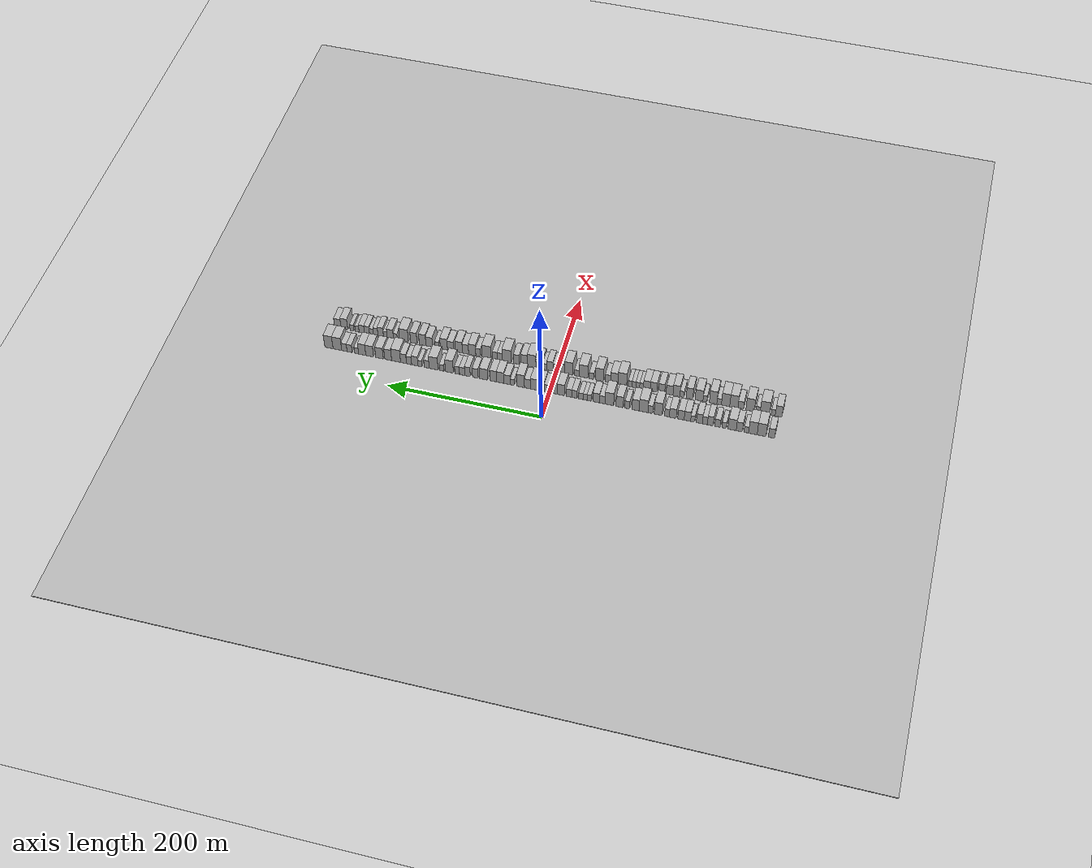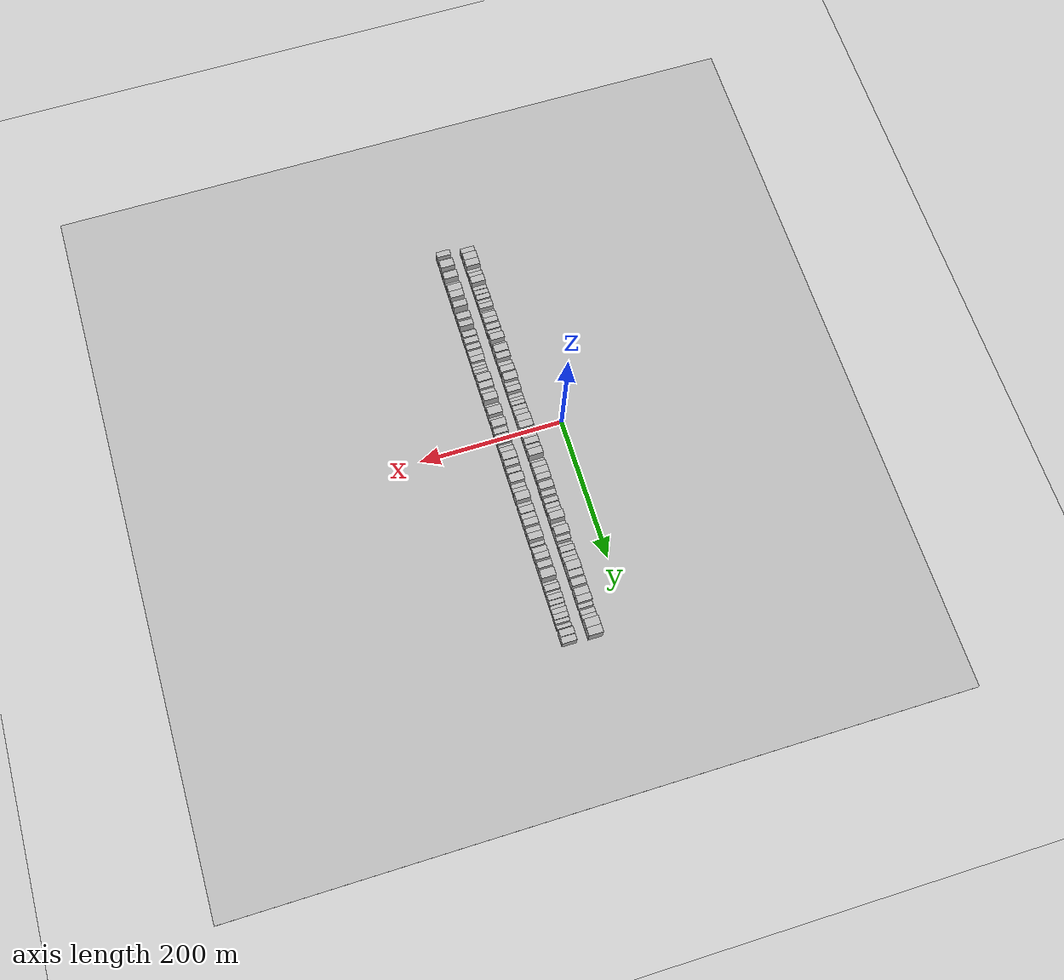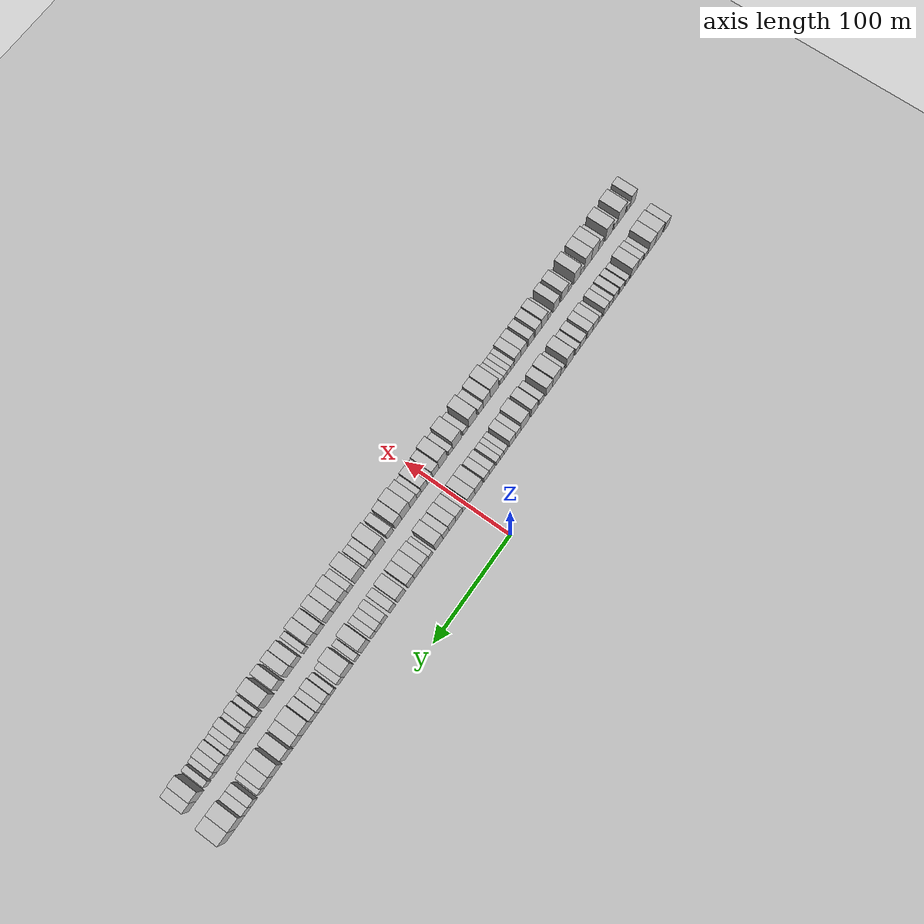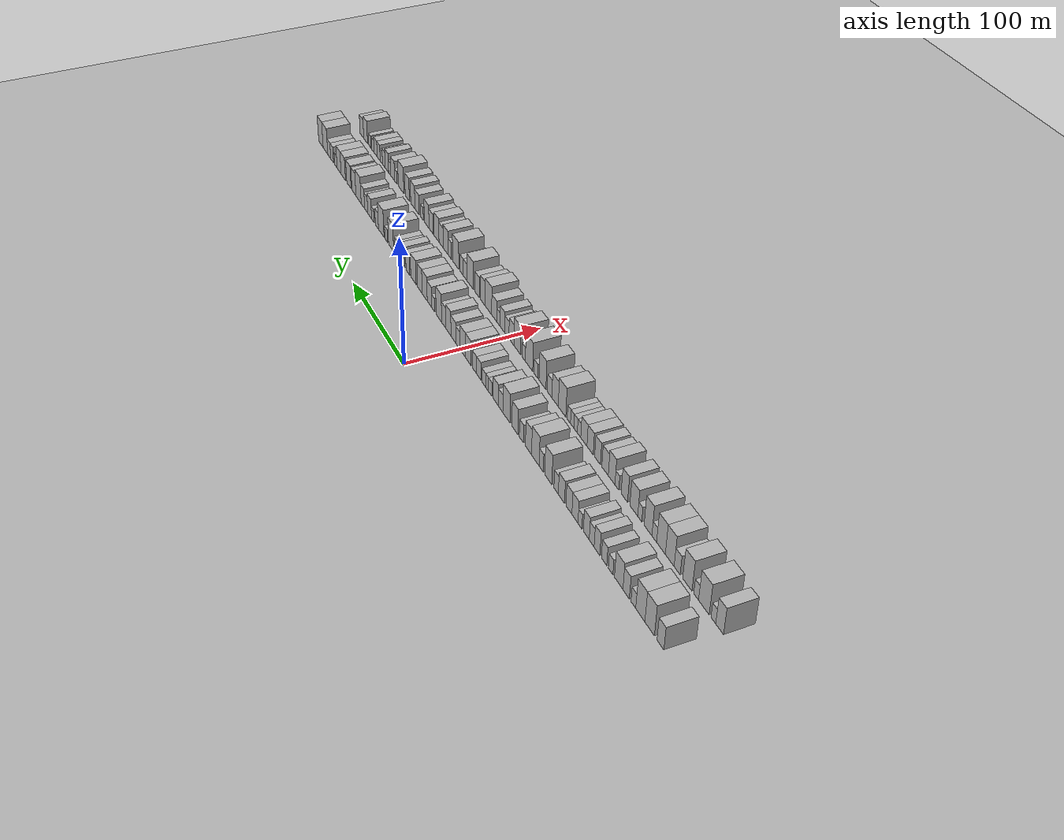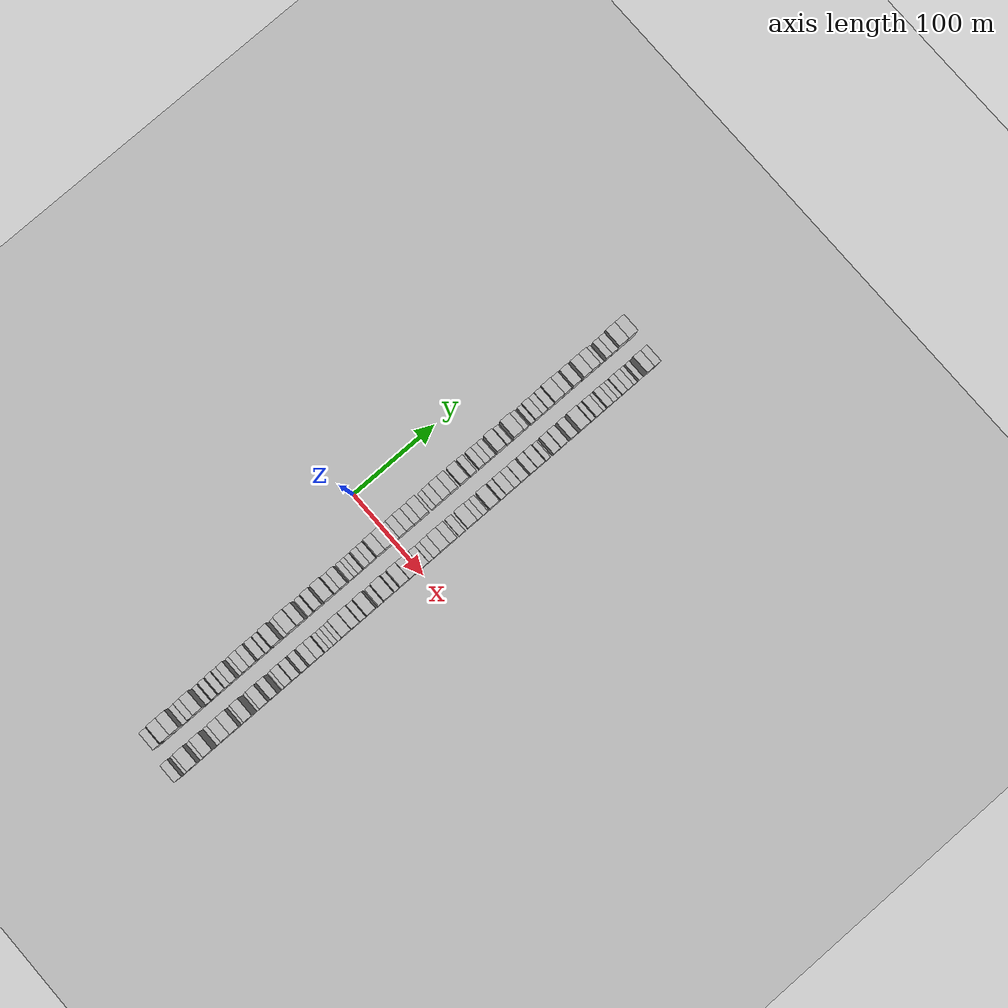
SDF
<?xml version="1.0" encoding="utf-8"?>

<sdf version="1.6">

   <world name="default">

      <gui fullscreen="0">

         <camera name="user_camera">

            <pose>-15 0 4.57585 0 0 0</pose>

            <view_controller>orbit</view_controller>

         </camera>

      </gui>

      <scene>

         <sky>

           <clouds>

             <speed>12</speed>

           </clouds>

         </sky>

         <ambient>0.4 0.4 0.4 1</ambient>

         <background>0.7 0.7 0.7 1</background>

         <shadows>1</shadows>

      </scene>

      <gravity>0 0 -9.8066</gravity>

      <magnetic_field>6e-06 2.3e-05 -4.2e-05</magnetic_field>

      <physics default="0" name="default_physics" type="ode">

         <ode>

            <solver>

               <type>quick</type>

               <iters>10</iters>

               <sor>1.0</sor>

               <use_dynamic_moi_rescaling>0</use_dynamic_moi_rescaling>

            </solver>

            <constraints>

               <cfm>0</cfm>

               <erp>0.2</erp>

               <contact_max_correcting_vel>100</contact_max_correcting_vel>

               <contact_surface_layer>0.001</contact_surface_layer>

            </constraints>

         </ode>

         <max_step_size>0.004</max_step_size>

         <real_time_factor>1</real_time_factor>

         <real_time_update_rate>250</real_time_update_rate>

      </physics>

      <light name="sun" type="directional">

         <cast_shadows>1</cast_shadows>

         <pose>0 0 10 0 0 0</pose>

         <diffuse>0.8 0.8 0.8 1</diffuse>

         <specular>0.2 0.2 0.2 1</specular>

         <attenuation>

            <range>1000</range>

            <constant>0.9</constant>

            <linear>0.01</linear>

            <quadratic>0.001</quadratic>

         </attenuation>

         <direction>-0.5 0.1 -0.9</direction>

      </light>

      <include>

         <name>ground_plane_1</name>

         <uri>model://HANNAS_ground_plane</uri>

         <pose>0 0 0  0 0 0</pose>

      </include>

      <include>

         <name>ground_plane_2</name>

         <uri>model://HANNAS_ground_plane</uri>

         <pose>100 0 0  0 0 0</pose>

      </include>

      <model name="building_1">

         <static>1</static>

         <pose frame="">50.0000 -283.1225 0 0.000000 0.000000 0.000000</pose>

         <link name="link">

            <pose frame="">0 0 9.00 0 0 0</pose>

            <collision name="collision">

               <geometry>

                  <box>

                     <size>20.0000 7.7550 18.0000</size>

                  </box>

               </geometry>

               <max_contacts>10</max_contacts>

               <surface>

                  <contact>

                     <ode/>

                  </contact>

                  <bounce/>

                  <friction>

                     <torsional>

                        <ode/>

                     </torsional>

                     <ode/>

                  </friction>

               </surface>

            </collision>

            <visual name="visual">

               <cast_shadows>0</cast_shadows>

               <geometry>

                  <box>

                     <size>20.0000 7.7550 18.0000</size>

                  </box>

               </geometry>

               <material>

                  <script>

                     <uri>model://HANNAS_wall/materials/scripts</uri>

                     <uri>model://HANNAS_wall/materials/textures</uri>

                     <name>vrc/HANNAS_wall</name>

                  </script>

               </material>

            </visual>

            <self_collide>0</self_collide>

            <enable_wind>0</enable_wind>

            <kinematic>0</kinematic>

         </link>

      </model>

      <model name="building_2">

         <static>1</static>

         <pose frame="">50.0000 -270.7268 0 0.000000 0.000000 0.000000</pose>

         <link name="link">

            <pose frame="">0 0 12.00 0 0 0</pose>

            <collision name="collision">

               <geometry>

                  <box>

                     <size>20.0000 11.0365 24.0000</size>

                  </box>

               </geometry>

               <max_contacts>10</max_contacts>

               <surface>

                  <contact>

                     <ode/>

                  </contact>

                  <bounce/>

                  <friction>

                     <torsional>

                        <ode/>

                     </torsional>

                     <ode/>

                  </friction>

               </surface>

            </collision>

            <visual name="visual">

               <cast_shadows>0</cast_shadows>

               <geometry>

                  <box>

                     <size>20.0000 11.0365 24.0000</size>

                  </box>

               </geometry>

               <material>

                  <script>

                     <uri>model://HANNAS_wall/materials/scripts</uri>

                     <uri>model://HANNAS_wall/materials/textures</uri>

                     <name>vrc/HANNAS_wall</name>

                  </script>

               </material>

            </visual>

            <self_collide>0</self_collide>

            <enable_wind>0</enable_wind>

            <kinematic>0</kinematic>

         </link>

      </model>

      <model name="building_3">

         <static>1</static>

         <pose frame="">50.0000 -259.8181 0 0.000000 0.000000 0.000000</pose>

         <link name="link">

            <pose frame="">0 0 12.00 0 0 0</pose>

            <collision name="collision">

               <geometry>

                  <box>

                     <size>20.0000 10.7809 24.0000</size>

                  </box>

               </geometry>

               <max_contacts>10</max_contacts>

               <surface>

                  <contact>

                     <ode/>

                  </contact>

                  <bounce/>

                  <friction>

                     <torsional>

                        <ode/>

                     </torsional>

                     <ode/>

                  </friction>

               </surface>

            </collision>

            <visual name="visual">

               <cast_shadows>0</cast_shadows>

               <geometry>

                  <box>

                     <size>20.0000 10.7809 24.0000</size>

                  </box>

               </geometry>

               <material>

                  <script>

                     <uri>model://HANNAS_wall/materials/scripts</uri>

                     <uri>model://HANNAS_wall/materials/textures</uri>

                     <name>vrc/HANNAS_wall</name>

                  </script>

               </material>

            </visual>

            <self_collide>0</self_collide>

            <enable_wind>0</enable_wind>

            <kinematic>0</kinematic>

         </link>

      </model>

      <model name="building_4">

         <static>1</static>

         <pose frame="">50.0000 -251.5832 0 0.000000 0.000000 0.000000</pose>

         <link name="link">

            <pose frame="">0 0 6.00 0 0 0</pose>

            <collision name="collision">

               <geometry>

                  <box>

                     <size>20.0000 5.6888 12.0000</size>

                  </box>

               </geometry>

               <max_contacts>10</max_contacts>

               <surface>

                  <contact>

                     <ode/>

                  </contact>

                  <bounce/>

                  <friction>

                     <torsional>

                        <ode/>

                     </torsional>

                     <ode/>

                  </friction>

               </surface>

            </collision>

            <visual name="visual">

               <cast_shadows>0</cast_shadows>

               <geometry>

                  <box>

                     <size>20.0000 5.6888 12.0000</size>

                  </box>

               </geometry>

               <material>

                  <script>

                     <uri>model://HANNAS_wall/materials/scripts</uri>

                     <uri>model://HANNAS_wall/materials/textures</uri>

                     <name>vrc/HANNAS_wall</name>

                  </script>

               </material>

            </visual>

            <self_collide>0</self_collide>

            <enable_wind>0</enable_wind>

            <kinematic>0</kinematic>

         </link>

      </model>

      <model name="building_5">

         <static>1</static>

         <pose frame="">50.0000 -242.8581 0 0.000000 0.000000 0.000000</pose>

         <link name="link">

            <pose frame="">0 0 9.00 0 0 0</pose>

            <collision name="collision">

               <geometry>

                  <box>

                     <size>20.0000 7.7615 18.0000</size>

                  </box>

               </geometry>

               <max_contacts>10</max_contacts>

               <surface>

                  <contact>

                     <ode/>

                  </contact>

                  <bounce/>

                  <friction>

                     <torsional>

                        <ode/>

                     </torsional>

                     <ode/>

                  </friction>

               </surface>

            </collision>

            <visual name="visual">

               <cast_shadows>0</cast_shadows>

               <geometry>

                  <box>

                     <size>20.0000 7.7615 18.0000</size>

                  </box>

               </geometry>

               <material>

                  <script>

                     <uri>model://HANNAS_wall/materials/scripts</uri>

                     <uri>model://HANNAS_wall/materials/textures</uri>

                     <name>vrc/HANNAS_wall</name>

                  </script>

               </material>

            </visual>

            <self_collide>0</self_collide>

            <enable_wind>0</enable_wind>

            <kinematic>0</kinematic>

         </link>

      </model>

      <model name="building_6">

         <static>1</static>

         <pose frame="">50.0000 -233.7783 0 0.000000 0.000000 0.000000</pose>

         <link name="link">

            <pose frame="">0 0 10.50 0 0 0</pose>

            <collision name="collision">

               <geometry>

                  <box>

                     <size>20.0000 10.3982 21.0000</size>

                  </box>

               </geometry>

               <max_contacts>10</max_contacts>

               <surface>

                  <contact>

                     <ode/>

                  </contact>

                  <bounce/>

                  <friction>

                     <torsional>

                        <ode/>

                     </torsional>

                     <ode/>

                  </friction>

               </surface>

            </collision>

            <visual name="visual">

               <cast_shadows>0</cast_shadows>

               <geometry>

                  <box>

                     <size>20.0000 10.3982 21.0000</size>

                  </box>

               </geometry>

               <material>

                  <script>

                     <uri>model://HANNAS_wall/materials/scripts</uri>

                     <uri>model://HANNAS_wall/materials/textures</uri>

                     <name>vrc/HANNAS_wall</name>

                  </script>

               </material>

            </visual>

            <self_collide>0</self_collide>

            <enable_wind>0</enable_wind>

            <kinematic>0</kinematic>

         </link>

      </model>

      <model name="building_7">

         <static>1</static>

         <pose frame="">50.0000 -223.7424 0 0.000000 0.000000 0.000000</pose>

         <link name="link">

            <pose frame="">0 0 6.00 0 0 0</pose>

            <collision name="collision">

               <geometry>

                  <box>

                     <size>20.0000 5.6735 12.0000</size>

                  </box>

               </geometry>

               <max_contacts>10</max_contacts>

               <surface>

                  <contact>

                     <ode/>

                  </contact>

                  <bounce/>

                  <friction>

                     <torsional>

                        <ode/>

                     </torsional>

                     <ode/>

                  </friction>

               </surface>

            </collision>

            <visual name="visual">

               <cast_shadows>0</cast_shadows>

               <geometry>

                  <box>

                     <size>20.0000 5.6735 12.0000</size>

                  </box>

               </geometry>

               <material>

                  <script>

                     <uri>model://HANNAS_wall/materials/scripts</uri>

                     <uri>model://HANNAS_wall/materials/textures</uri>

                     <name>vrc/HANNAS_wall</name>

                  </script>

               </material>

            </visual>

            <self_collide>0</self_collide>

            <enable_wind>0</enable_wind>

            <kinematic>0</kinematic>

         </link>

      </model>

      <model name="building_8">

         <static>1</static>

         <pose frame="">50.0000 -215.4762 0 0.000000 0.000000 0.000000</pose>

         <link name="link">

            <pose frame="">0 0 7.50 0 0 0</pose>

            <collision name="collision">

               <geometry>

                  <box>

                     <size>20.0000 6.8589 15.0000</size>

                  </box>

               </geometry>

               <max_contacts>10</max_contacts>

               <surface>

                  <contact>

                     <ode/>

                  </contact>

                  <bounce/>

                  <friction>

                     <torsional>

                        <ode/>

                     </torsional>

                     <ode/>

                  </friction>

               </surface>

            </collision>

            <visual name="visual">

               <cast_shadows>0</cast_shadows>

               <geometry>

                  <box>

                     <size>20.0000 6.8589 15.0000</size>

                  </box>

               </geometry>

               <material>

                  <script>

                     <uri>model://HANNAS_wall/materials/scripts</uri>

                     <uri>model://HANNAS_wall/materials/textures</uri>

                     <name>vrc/HANNAS_wall</name>

                  </script>

               </material>

            </visual>

            <self_collide>0</self_collide>

            <enable_wind>0</enable_wind>

            <kinematic>0</kinematic>

         </link>

      </model>

      <model name="building_9">

         <static>1</static>

         <pose frame="">50.0000 -206.3850 0 0.000000 0.000000 0.000000</pose>

         <link name="link">

            <pose frame="">0 0 9.00 0 0 0</pose>

            <collision name="collision">

               <geometry>

                  <box>

                     <size>20.0000 7.3234 18.0000</size>

                  </box>

               </geometry>

               <max_contacts>10</max_contacts>

               <surface>

                  <contact>

                     <ode/>

                  </contact>

                  <bounce/>

                  <friction>

                     <torsional>

                        <ode/>

                     </torsional>

                     <ode/>

                  </friction>

               </surface>

            </collision>

            <visual name="visual">

               <cast_shadows>0</cast_shadows>

               <geometry>

                  <box>

                     <size>20.0000 7.3234 18.0000</size>

                  </box>

               </geometry>

               <material>

                  <script>

                     <uri>model://HANNAS_wall/materials/scripts</uri>

                     <uri>model://HANNAS_wall/materials/textures</uri>

                     <name>vrc/HANNAS_wall</name>

                  </script>

               </material>

            </visual>

            <self_collide>0</self_collide>

            <enable_wind>0</enable_wind>

            <kinematic>0</kinematic>

         </link>

      </model>

      <model name="building_10">

         <static>1</static>

         <pose frame="">50.0000 -199.5266 0 0.000000 0.000000 0.000000</pose>

         <link name="link">

            <pose frame="">0 0 7.50 0 0 0</pose>

            <collision name="collision">

               <geometry>

                  <box>

                     <size>20.0000 6.3935 15.0000</size>

                  </box>

               </geometry>

               <max_contacts>10</max_contacts>

               <surface>

                  <contact>

                     <ode/>

                  </contact>

                  <bounce/>

                  <friction>

                     <torsional>

                        <ode/>

                     </torsional>

                     <ode/>

                  </friction>

               </surface>

            </collision>

            <visual name="visual">

               <cast_shadows>0</cast_shadows>

               <geometry>

                  <box>

                     <size>20.0000 6.3935 15.0000</size>

                  </box>

               </geometry>

               <material>

                  <script>

                     <uri>model://HANNAS_wall/materials/scripts</uri>

                     <uri>model://HANNAS_wall/materials/textures</uri>

                     <name>vrc/HANNAS_wall</name>

                  </script>

               </material>

            </visual>

            <self_collide>0</self_collide>

            <enable_wind>0</enable_wind>

            <kinematic>0</kinematic>

         </link>

      </model>

      <model name="building_11">

         <static>1</static>

         <pose frame="">50.0000 -192.4735 0 0.000000 0.000000 0.000000</pose>

         <link name="link">

            <pose frame="">0 0 9.00 0 0 0</pose>

            <collision name="collision">

               <geometry>

                  <box>

                     <size>20.0000 7.7126 18.0000</size>

                  </box>

               </geometry>

               <max_contacts>10</max_contacts>

               <surface>

                  <contact>

                     <ode/>

                  </contact>

                  <bounce/>

                  <friction>

                     <torsional>

                        <ode/>

                     </torsional>

                     <ode/>

                  </friction>

               </surface>

            </collision>

            <visual name="visual">

               <cast_shadows>0</cast_shadows>

               <geometry>

                  <box>

                     <size>20.0000 7.7126 18.0000</size>

                  </box>

               </geometry>

               <material>

                  <script>

                     <uri>model://HANNAS_wall/materials/scripts</uri>

                     <uri>model://HANNAS_wall/materials/textures</uri>

                     <name>vrc/HANNAS_wall</name>

                  </script>

               </material>

            </visual>

            <self_collide>0</self_collide>

            <enable_wind>0</enable_wind>

            <kinematic>0</kinematic>

         </link>

      </model>

      <model name="building_12">

         <static>1</static>

         <pose frame="">50.0000 -184.0339 0 0.000000 0.000000 0.000000</pose>

         <link name="link">

            <pose frame="">0 0 6.00 0 0 0</pose>

            <collision name="collision">

               <geometry>

                  <box>

                     <size>20.0000 5.1668 12.0000</size>

                  </box>

               </geometry>

               <max_contacts>10</max_contacts>

               <surface>

                  <contact>

                     <ode/>

                  </contact>

                  <bounce/>

                  <friction>

                     <torsional>

                        <ode/>

                     </torsional>

                     <ode/>

                  </friction>

               </surface>

            </collision>

            <visual name="visual">

               <cast_shadows>0</cast_shadows>

               <geometry>

                  <box>

                     <size>20.0000 5.1668 12.0000</size>

                  </box>

               </geometry>

               <material>

                  <script>

                     <uri>model://HANNAS_wall/materials/scripts</uri>

                     <uri>model://HANNAS_wall/materials/textures</uri>

                     <name>vrc/HANNAS_wall</name>

                  </script>

               </material>

            </visual>

            <self_collide>0</self_collide>

            <enable_wind>0</enable_wind>

            <kinematic>0</kinematic>

         </link>

      </model>

      <model name="building_13">

         <static>1</static>

         <pose frame="">50.0000 -177.3395 0 0.000000 0.000000 0.000000</pose>

         <link name="link">

            <pose frame="">0 0 9.00 0 0 0</pose>

            <collision name="collision">

               <geometry>

                  <box>

                     <size>20.0000 8.2220 18.0000</size>

                  </box>

               </geometry>

               <max_contacts>10</max_contacts>

               <surface>

                  <contact>

                     <ode/>

                  </contact>

                  <bounce/>

                  <friction>

                     <torsional>

                        <ode/>

                     </torsional>

                     <ode/>

                  </friction>

               </surface>

            </collision>

            <visual name="visual">

               <cast_shadows>0</cast_shadows>

               <geometry>

                  <box>

                     <size>20.0000 8.2220 18.0000</size>

                  </box>

               </geometry>

               <material>

                  <script>

                     <uri>model://HANNAS_wall/materials/scripts</uri>

                     <uri>model://HANNAS_wall/materials/textures</uri>

                     <name>vrc/HANNAS_wall</name>

                  </script>

               </material>

            </visual>

            <self_collide>0</self_collide>

            <enable_wind>0</enable_wind>

            <kinematic>0</kinematic>

         </link>

      </model>

      <model name="building_14">

         <static>1</static>

         <pose frame="">50.0000 -169.1463 0 0.000000 0.000000 0.000000</pose>

         <link name="link">

            <pose frame="">0 0 9.00 0 0 0</pose>

            <collision name="collision">

               <geometry>

                  <box>

                     <size>20.0000 8.1645 18.0000</size>

                  </box>

               </geometry>

               <max_contacts>10</max_contacts>

               <surface>

                  <contact>

                     <ode/>

                  </contact>

                  <bounce/>

                  <friction>

                     <torsional>

                        <ode/>

                     </torsional>

                     <ode/>

                  </friction>

               </surface>

            </collision>

            <visual name="visual">

               <cast_shadows>0</cast_shadows>

               <geometry>

                  <box>

                     <size>20.0000 8.1645 18.0000</size>

                  </box>

               </geometry>

               <material>

                  <script>

                     <uri>model://HANNAS_wall/materials/scripts</uri>

                     <uri>model://HANNAS_wall/materials/textures</uri>

                     <name>vrc/HANNAS_wall</name>

                  </script>

               </material>

            </visual>

            <self_collide>0</self_collide>

            <enable_wind>0</enable_wind>

            <kinematic>0</kinematic>

         </link>

      </model>

      <model name="building_15">

         <static>1</static>

         <pose frame="">50.0000 -158.7706 0 0.000000 0.000000 0.000000</pose>

         <link name="link">

            <pose frame="">0 0 9.00 0 0 0</pose>

            <collision name="collision">

               <geometry>

                  <box>

                     <size>20.0000 8.5869 18.0000</size>

                  </box>

               </geometry>

               <max_contacts>10</max_contacts>

               <surface>

                  <contact>

                     <ode/>

                  </contact>

                  <bounce/>

                  <friction>

                     <torsional>

                        <ode/>

                     </torsional>

                     <ode/>

                  </friction>

               </surface>

            </collision>

            <visual name="visual">

               <cast_shadows>0</cast_shadows>

               <geometry>

                  <box>

                     <size>20.0000 8.5869 18.0000</size>

                  </box>

               </geometry>

               <material>

                  <script>

                     <uri>model://HANNAS_wall/materials/scripts</uri>

                     <uri>model://HANNAS_wall/materials/textures</uri>

                     <name>vrc/HANNAS_wall</name>

                  </script>

               </material>

            </visual>

            <self_collide>0</self_collide>

            <enable_wind>0</enable_wind>

            <kinematic>0</kinematic>

         </link>

      </model>

      <model name="building_16">

         <static>1</static>

         <pose frame="">50.0000 -151.3988 0 0.000000 0.000000 0.000000</pose>

         <link name="link">

            <pose frame="">0 0 7.50 0 0 0</pose>

            <collision name="collision">

               <geometry>

                  <box>

                     <size>20.0000 6.1567 15.0000</size>

                  </box>

               </geometry>

               <max_contacts>10</max_contacts>

               <surface>

                  <contact>

                     <ode/>

                  </contact>

                  <bounce/>

                  <friction>

                     <torsional>

                        <ode/>

                     </torsional>

                     <ode/>

                  </friction>

               </surface>

            </collision>

            <visual name="visual">

               <cast_shadows>0</cast_shadows>

               <geometry>

                  <box>

                     <size>20.0000 6.1567 15.0000</size>

                  </box>

               </geometry>

               <material>

                  <script>

                     <uri>model://HANNAS_wall/materials/scripts</uri>

                     <uri>model://HANNAS_wall/materials/textures</uri>

                     <name>vrc/HANNAS_wall</name>

                  </script>

               </material>

            </visual>

            <self_collide>0</self_collide>

            <enable_wind>0</enable_wind>

            <kinematic>0</kinematic>

         </link>

      </model>

      <model name="building_17">

         <static>1</static>

         <pose frame="">50.0000 -140.2153 0 0.000000 0.000000 0.000000</pose>

         <link name="link">

            <pose frame="">0 0 12.00 0 0 0</pose>

            <collision name="collision">

               <geometry>

                  <box>

                     <size>20.0000 10.2103 24.0000</size>

                  </box>

               </geometry>

               <max_contacts>10</max_contacts>

               <surface>

                  <contact>

                     <ode/>

                  </contact>

                  <bounce/>

                  <friction>

                     <torsional>

                        <ode/>

                     </torsional>

                     <ode/>

                  </friction>

               </surface>

            </collision>

            <visual name="visual">

               <cast_shadows>0</cast_shadows>

               <geometry>

                  <box>

                     <size>20.0000 10.2103 24.0000</size>

                  </box>

               </geometry>

               <material>

                  <script>

                     <uri>model://HANNAS_wall/materials/scripts</uri>

                     <uri>model://HANNAS_wall/materials/textures</uri>

                     <name>vrc/HANNAS_wall</name>

                  </script>

               </material>

            </visual>

            <self_collide>0</self_collide>

            <enable_wind>0</enable_wind>

            <kinematic>0</kinematic>

         </link>

      </model>

      <model name="building_18">

         <static>1</static>

         <pose frame="">50.0000 -130.0983 0 0.000000 0.000000 0.000000</pose>

         <link name="link">

            <pose frame="">0 0 7.50 0 0 0</pose>

            <collision name="collision">

               <geometry>

                  <box>

                     <size>20.0000 6.0237 15.0000</size>

                  </box>

               </geometry>

               <max_contacts>10</max_contacts>

               <surface>

                  <contact>

                     <ode/>

                  </contact>

                  <bounce/>

                  <friction>

                     <torsional>

                        <ode/>

                     </torsional>

                     <ode/>

                  </friction>

               </surface>

            </collision>

            <visual name="visual">

               <cast_shadows>0</cast_shadows>

               <geometry>

                  <box>

                     <size>20.0000 6.0237 15.0000</size>

                  </box>

               </geometry>

               <material>

                  <script>

                     <uri>model://HANNAS_wall/materials/scripts</uri>

                     <uri>model://HANNAS_wall/materials/textures</uri>

                     <name>vrc/HANNAS_wall</name>

                  </script>

               </material>

            </visual>

            <self_collide>0</self_collide>

            <enable_wind>0</enable_wind>

            <kinematic>0</kinematic>

         </link>

      </model>

      <model name="building_19">

         <static>1</static>

         <pose frame="">50.0000 -121.5091 0 0.000000 0.000000 0.000000</pose>

         <link name="link">

            <pose frame="">0 0 12.00 0 0 0</pose>

            <collision name="collision">

               <geometry>

                  <box>

                     <size>20.0000 11.1546 24.0000</size>

                  </box>

               </geometry>

               <max_contacts>10</max_contacts>

               <surface>

                  <contact>

                     <ode/>

                  </contact>

                  <bounce/>

                  <friction>

                     <torsional>

                        <ode/>

                     </torsional>

                     <ode/>

                  </friction>

               </surface>

            </collision>

            <visual name="visual">

               <cast_shadows>0</cast_shadows>

               <geometry>

                  <box>

                     <size>20.0000 11.1546 24.0000</size>

                  </box>

               </geometry>

               <material>

                  <script>

                     <uri>model://HANNAS_wall/materials/scripts</uri>

                     <uri>model://HANNAS_wall/materials/textures</uri>

                     <name>vrc/HANNAS_wall</name>

                  </script>

               </material>

            </visual>

            <self_collide>0</self_collide>

            <enable_wind>0</enable_wind>

            <kinematic>0</kinematic>

         </link>

      </model>

      <model name="building_20">

         <static>1</static>

         <pose frame="">50.0000 -111.3665 0 0.000000 0.000000 0.000000</pose>

         <link name="link">

            <pose frame="">0 0 10.50 0 0 0</pose>

            <collision name="collision">

               <geometry>

                  <box>

                     <size>20.0000 9.1307 21.0000</size>

                  </box>

               </geometry>

               <max_contacts>10</max_contacts>

               <surface>

                  <contact>

                     <ode/>

                  </contact>

                  <bounce/>

                  <friction>

                     <torsional>

                        <ode/>

                     </torsional>

                     <ode/>

                  </friction>

               </surface>

            </collision>

            <visual name="visual">

               <cast_shadows>0</cast_shadows>

               <geometry>

                  <box>

                     <size>20.0000 9.1307 21.0000</size>

                  </box>

               </geometry>

               <material>

                  <script>

                     <uri>model://HANNAS_wall/materials/scripts</uri>

                     <uri>model://HANNAS_wall/materials/textures</uri>

                     <name>vrc/HANNAS_wall</name>

                  </script>

               </material>

            </visual>

            <self_collide>0</self_collide>

            <enable_wind>0</enable_wind>

            <kinematic>0</kinematic>

         </link>

      </model>

      <model name="building_21">

         <static>1</static>

         <pose frame="">50.0000 -100.6610 0 0.000000 0.000000 0.000000</pose>

         <link name="link">

            <pose frame="">0 0 7.50 0 0 0</pose>

            <collision name="collision">

               <geometry>

                  <box>

                     <size>20.0000 6.2802 15.0000</size>

                  </box>

               </geometry>

               <max_contacts>10</max_contacts>

               <surface>

                  <contact>

                     <ode/>

                  </contact>

                  <bounce/>

                  <friction>

                     <torsional>

                        <ode/>

                     </torsional>

                     <ode/>

                  </friction>

               </surface>

            </collision>

            <visual name="visual">

               <cast_shadows>0</cast_shadows>

               <geometry>

                  <box>

                     <size>20.0000 6.2802 15.0000</size>

                  </box>

               </geometry>

               <material>

                  <script>

                     <uri>model://HANNAS_wall/materials/scripts</uri>

                     <uri>model://HANNAS_wall/materials/textures</uri>

                     <name>vrc/HANNAS_wall</name>

                  </script>

               </material>

            </visual>

            <self_collide>0</self_collide>

            <enable_wind>0</enable_wind>

            <kinematic>0</kinematic>

         </link>

      </model>

      <model name="building_22">

         <static>1</static>

         <pose frame="">50.0000 -90.8468 0 0.000000 0.000000 0.000000</pose>

         <link name="link">

            <pose frame="">0 0 10.50 0 0 0</pose>

            <collision name="collision">

               <geometry>

                  <box>

                     <size>20.0000 9.3482 21.0000</size>

                  </box>

               </geometry>

               <max_contacts>10</max_contacts>

               <surface>

                  <contact>

                     <ode/>

                  </contact>

                  <bounce/>

                  <friction>

                     <torsional>

                        <ode/>

                     </torsional>

                     <ode/>

                  </friction>

               </surface>

            </collision>

            <visual name="visual">

               <cast_shadows>0</cast_shadows>

               <geometry>

                  <box>

                     <size>20.0000 9.3482 21.0000</size>

                  </box>

               </geometry>

               <material>

                  <script>

                     <uri>model://HANNAS_wall/materials/scripts</uri>

                     <uri>model://HANNAS_wall/materials/textures</uri>

                     <name>vrc/HANNAS_wall</name>

                  </script>

               </material>

            </visual>

            <self_collide>0</self_collide>

            <enable_wind>0</enable_wind>

            <kinematic>0</kinematic>

         </link>

      </model>

      <model name="building_23">

         <static>1</static>

         <pose frame="">50.0000 -77.5330 0 0.000000 0.000000 0.000000</pose>

         <link name="link">

            <pose frame="">0 0 12.00 0 0 0</pose>

            <collision name="collision">

               <geometry>

                  <box>

                     <size>20.0000 11.2795 24.0000</size>

                  </box>

               </geometry>

               <max_contacts>10</max_contacts>

               <surface>

                  <contact>

                     <ode/>

                  </contact>

                  <bounce/>

                  <friction>

                     <torsional>

                        <ode/>

                     </torsional>

                     <ode/>

                  </friction>

               </surface>

            </collision>

            <visual name="visual">

               <cast_shadows>0</cast_shadows>

               <geometry>

                  <box>

                     <size>20.0000 11.2795 24.0000</size>

                  </box>

               </geometry>

               <material>

                  <script>

                     <uri>model://HANNAS_wall/materials/scripts</uri>

                     <uri>model://HANNAS_wall/materials/textures</uri>

                     <name>vrc/HANNAS_wall</name>

                  </script>

               </material>

            </visual>

            <self_collide>0</self_collide>

            <enable_wind>0</enable_wind>

            <kinematic>0</kinematic>

         </link>

      </model>

      <model name="building_24">

         <static>1</static>

         <pose frame="">50.0000 -68.4396 0 0.000000 0.000000 0.000000</pose>

         <link name="link">

            <pose frame="">0 0 7.50 0 0 0</pose>

            <collision name="collision">

               <geometry>

                  <box>

                     <size>20.0000 6.9074 15.0000</size>

                  </box>

               </geometry>

               <max_contacts>10</max_contacts>

               <surface>

                  <contact>

                     <ode/>

                  </contact>

                  <bounce/>

                  <friction>

                     <torsional>

                        <ode/>

                     </torsional>

                     <ode/>

                  </friction>

               </surface>

            </collision>

            <visual name="visual">

               <cast_shadows>0</cast_shadows>

               <geometry>

                  <box>

                     <size>20.0000 6.9074 15.0000</size>

                  </box>

               </geometry>

               <material>

                  <script>

                     <uri>model://HANNAS_wall/materials/scripts</uri>

                     <uri>model://HANNAS_wall/materials/textures</uri>

                     <name>vrc/HANNAS_wall</name>

                  </script>

               </material>

            </visual>

            <self_collide>0</self_collide>

            <enable_wind>0</enable_wind>

            <kinematic>0</kinematic>

         </link>

      </model>

      <model name="building_25">

         <static>1</static>

         <pose frame="">50.0000 -60.6884 0 0.000000 0.000000 0.000000</pose>

         <link name="link">

            <pose frame="">0 0 9.00 0 0 0</pose>

            <collision name="collision">

               <geometry>

                  <box>

                     <size>20.0000 8.5951 18.0000</size>

                  </box>

               </geometry>

               <max_contacts>10</max_contacts>

               <surface>

                  <contact>

                     <ode/>

                  </contact>

                  <bounce/>

                  <friction>

                     <torsional>

                        <ode/>

                     </torsional>

                     <ode/>

                  </friction>

               </surface>

            </collision>

            <visual name="visual">

               <cast_shadows>0</cast_shadows>

               <geometry>

                  <box>

                     <size>20.0000 8.5951 18.0000</size>

                  </box>

               </geometry>

               <material>

                  <script>

                     <uri>model://HANNAS_wall/materials/scripts</uri>

                     <uri>model://HANNAS_wall/materials/textures</uri>

                     <name>vrc/HANNAS_wall</name>

                  </script>

               </material>

            </visual>

            <self_collide>0</self_collide>

            <enable_wind>0</enable_wind>

            <kinematic>0</kinematic>

         </link>

      </model>

      <model name="building_26">

         <static>1</static>

         <pose frame="">50.0000 -51.6435 0 0.000000 0.000000 0.000000</pose>

         <link name="link">

            <pose frame="">0 0 6.00 0 0 0</pose>

            <collision name="collision">

               <geometry>

                  <box>

                     <size>20.0000 5.4947 12.0000</size>

                  </box>

               </geometry>

               <max_contacts>10</max_contacts>

               <surface>

                  <contact>

                     <ode/>

                  </contact>

                  <bounce/>

                  <friction>

                     <torsional>

                        <ode/>

                     </torsional>

                     <ode/>

                  </friction>

               </surface>

            </collision>

            <visual name="visual">

               <cast_shadows>0</cast_shadows>

               <geometry>

                  <box>

                     <size>20.0000 5.4947 12.0000</size>

                  </box>

               </geometry>

               <material>

                  <script>

                     <uri>model://HANNAS_wall/materials/scripts</uri>

                     <uri>model://HANNAS_wall/materials/textures</uri>

                     <name>vrc/HANNAS_wall</name>

                  </script>

               </material>

            </visual>

            <self_collide>0</self_collide>

            <enable_wind>0</enable_wind>

            <kinematic>0</kinematic>

         </link>

      </model>

      <model name="building_27">

         <static>1</static>

         <pose frame="">50.0000 -46.4779 0 0.000000 0.000000 0.000000</pose>

         <link name="link">

            <pose frame="">0 0 6.00 0 0 0</pose>

            <collision name="collision">

               <geometry>

                  <box>

                     <size>20.0000 4.8365 12.0000</size>

                  </box>

               </geometry>

               <max_contacts>10</max_contacts>

               <surface>

                  <contact>

                     <ode/>

                  </contact>

                  <bounce/>

                  <friction>

                     <torsional>

                        <ode/>

                     </torsional>

                     <ode/>

                  </friction>

               </surface>

            </collision>

            <visual name="visual">

               <cast_shadows>0</cast_shadows>

               <geometry>

                  <box>

                     <size>20.0000 4.8365 12.0000</size>

                  </box>

               </geometry>

               <material>

                  <script>

                     <uri>model://HANNAS_wall/materials/scripts</uri>

                     <uri>model://HANNAS_wall/materials/textures</uri>

                     <name>vrc/HANNAS_wall</name>

                  </script>

               </material>

            </visual>

            <self_collide>0</self_collide>

            <enable_wind>0</enable_wind>

            <kinematic>0</kinematic>

         </link>

      </model>

      <model name="building_28">

         <static>1</static>

         <pose frame="">50.0000 -41.0760 0 0.000000 0.000000 0.000000</pose>

         <link name="link">

            <pose frame="">0 0 6.00 0 0 0</pose>

            <collision name="collision">

               <geometry>

                  <box>

                     <size>20.0000 5.9673 12.0000</size>

                  </box>

               </geometry>

               <max_contacts>10</max_contacts>

               <surface>

                  <contact>

                     <ode/>

                  </contact>

                  <bounce/>

                  <friction>

                     <torsional>

                        <ode/>

                     </torsional>

                     <ode/>

                  </friction>

               </surface>

            </collision>

            <visual name="visual">

               <cast_shadows>0</cast_shadows>

               <geometry>

                  <box>

                     <size>20.0000 5.9673 12.0000</size>

                  </box>

               </geometry>

               <material>

                  <script>

                     <uri>model://HANNAS_wall/materials/scripts</uri>

                     <uri>model://HANNAS_wall/materials/textures</uri>

                     <name>vrc/HANNAS_wall</name>

                  </script>

               </material>

            </visual>

            <self_collide>0</self_collide>

            <enable_wind>0</enable_wind>

            <kinematic>0</kinematic>

         </link>

      </model>

      <model name="building_29">

         <static>1</static>

         <pose frame="">50.0000 -32.6428 0 0.000000 0.000000 0.000000</pose>

         <link name="link">

            <pose frame="">0 0 7.50 0 0 0</pose>

            <collision name="collision">

               <geometry>

                  <box>

                     <size>20.0000 6.8992 15.0000</size>

                  </box>

               </geometry>

               <max_contacts>10</max_contacts>

               <surface>

                  <contact>

                     <ode/>

                  </contact>

                  <bounce/>

                  <friction>

                     <torsional>

                        <ode/>

                     </torsional>

                     <ode/>

                  </friction>

               </surface>

            </collision>

            <visual name="visual">

               <cast_shadows>0</cast_shadows>

               <geometry>

                  <box>

                     <size>20.0000 6.8992 15.0000</size>

                  </box>

               </geometry>

               <material>

                  <script>

                     <uri>model://HANNAS_wall/materials/scripts</uri>

                     <uri>model://HANNAS_wall/materials/textures</uri>

                     <name>vrc/HANNAS_wall</name>

                  </script>

               </material>

            </visual>

            <self_collide>0</self_collide>

            <enable_wind>0</enable_wind>

            <kinematic>0</kinematic>

         </link>

      </model>

      <model name="building_30">

         <static>1</static>

         <pose frame="">50.0000 -25.5044 0 0.000000 0.000000 0.000000</pose>

         <link name="link">

            <pose frame="">0 0 7.50 0 0 0</pose>

            <collision name="collision">

               <geometry>

                  <box>

                     <size>20.0000 7.3777 15.0000</size>

                  </box>

               </geometry>

               <max_contacts>10</max_contacts>

               <surface>

                  <contact>

                     <ode/>

                  </contact>

                  <bounce/>

                  <friction>

                     <torsional>

                        <ode/>

                     </torsional>

                     <ode/>

                  </friction>

               </surface>

            </collision>

            <visual name="visual">

               <cast_shadows>0</cast_shadows>

               <geometry>

                  <box>

                     <size>20.0000 7.3777 15.0000</size>

                  </box>

               </geometry>

               <material>

                  <script>

                     <uri>model://HANNAS_wall/materials/scripts</uri>

                     <uri>model://HANNAS_wall/materials/textures</uri>

                     <name>vrc/HANNAS_wall</name>

                  </script>

               </material>

            </visual>

            <self_collide>0</self_collide>

            <enable_wind>0</enable_wind>

            <kinematic>0</kinematic>

         </link>

      </model>

      <model name="building_31">

         <static>1</static>

         <pose frame="">50.0000 -14.9525 0 0.000000 0.000000 0.000000</pose>

         <link name="link">

            <pose frame="">0 0 10.50 0 0 0</pose>

            <collision name="collision">

               <geometry>

                  <box>

                     <size>20.0000 9.7260 21.0000</size>

                  </box>

               </geometry>

               <max_contacts>10</max_contacts>

               <surface>

                  <contact>

                     <ode/>

                  </contact>

                  <bounce/>

                  <friction>

                     <torsional>

                        <ode/>

                     </torsional>

                     <ode/>

                  </friction>

               </surface>

            </collision>

            <visual name="visual">

               <cast_shadows>0</cast_shadows>

               <geometry>

                  <box>

                     <size>20.0000 9.7260 21.0000</size>

                  </box>

               </geometry>

               <material>

                  <script>

                     <uri>model://HANNAS_wall/materials/scripts</uri>

                     <uri>model://HANNAS_wall/materials/textures</uri>

                     <name>vrc/HANNAS_wall</name>

                  </script>

               </material>

            </visual>

            <self_collide>0</self_collide>

            <enable_wind>0</enable_wind>

            <kinematic>0</kinematic>

         </link>

      </model>

      <model name="building_32">

         <static>1</static>

         <pose frame="">50.0000 -5.2037 0 0.000000 0.000000 0.000000</pose>

         <link name="link">

            <pose frame="">0 0 10.50 0 0 0</pose>

            <collision name="collision">

               <geometry>

                  <box>

                     <size>20.0000 9.7716 21.0000</size>

                  </box>

               </geometry>

               <max_contacts>10</max_contacts>

               <surface>

                  <contact>

                     <ode/>

                  </contact>

                  <bounce/>

                  <friction>

                     <torsional>

                        <ode/>

                     </torsional>

                     <ode/>

                  </friction>

               </surface>

            </collision>

            <visual name="visual">

               <cast_shadows>0</cast_shadows>

               <geometry>

                  <box>

                     <size>20.0000 9.7716 21.0000</size>

                  </box>

               </geometry>

               <material>

                  <script>

                     <uri>model://HANNAS_wall/materials/scripts</uri>

                     <uri>model://HANNAS_wall/materials/textures</uri>

                     <name>vrc/HANNAS_wall</name>

                  </script>

               </material>

            </visual>

            <self_collide>0</self_collide>

            <enable_wind>0</enable_wind>

            <kinematic>0</kinematic>

         </link>

      </model>

      <model name="building_33">

         <static>1</static>

         <pose frame="">50.0000 3.1521 0 0.000000 0.000000 0.000000</pose>

         <link name="link">

            <pose frame="">0 0 7.50 0 0 0</pose>

            <collision name="collision">

               <geometry>

                  <box>

                     <size>20.0000 6.9400 15.0000</size>

                  </box>

               </geometry>

               <max_contacts>10</max_contacts>

               <surface>

                  <contact>

                     <ode/>

                  </contact>

                  <bounce/>

                  <friction>

                     <torsional>

                        <ode/>

                     </torsional>

                     <ode/>

                  </friction>

               </surface>

            </collision>

            <visual name="visual">

               <cast_shadows>0</cast_shadows>

               <geometry>

                  <box>

                     <size>20.0000 6.9400 15.0000</size>

                  </box>

               </geometry>

               <material>

                  <script>

                     <uri>model://HANNAS_wall/materials/scripts</uri>

                     <uri>model://HANNAS_wall/materials/textures</uri>

                     <name>vrc/HANNAS_wall</name>

                  </script>

               </material>

            </visual>

            <self_collide>0</self_collide>

            <enable_wind>0</enable_wind>

            <kinematic>0</kinematic>

         </link>

      </model>

      <model name="building_34">

         <static>1</static>

         <pose frame="">50.0000 11.0460 0 0.000000 0.000000 0.000000</pose>

         <link name="link">

            <pose frame="">0 0 9.00 0 0 0</pose>

            <collision name="collision">

               <geometry>

                  <box>

                     <size>20.0000 8.8478 18.0000</size>

                  </box>

               </geometry>

               <max_contacts>10</max_contacts>

               <surface>

                  <contact>

                     <ode/>

                  </contact>

                  <bounce/>

                  <friction>

                     <torsional>

                        <ode/>

                     </torsional>

                     <ode/>

                  </friction>

               </surface>

            </collision>

            <visual name="visual">

               <cast_shadows>0</cast_shadows>

               <geometry>

                  <box>

                     <size>20.0000 8.8478 18.0000</size>

                  </box>

               </geometry>

               <material>

                  <script>

                     <uri>model://HANNAS_wall/materials/scripts</uri>

                     <uri>model://HANNAS_wall/materials/textures</uri>

                     <name>vrc/HANNAS_wall</name>

                  </script>

               </material>

            </visual>

            <self_collide>0</self_collide>

            <enable_wind>0</enable_wind>

            <kinematic>0</kinematic>

         </link>

      </model>

      <model name="building_35">

         <static>1</static>

         <pose frame="">50.0000 20.0284 0 0.000000 0.000000 0.000000</pose>

         <link name="link">

            <pose frame="">0 0 10.50 0 0 0</pose>

            <collision name="collision">

               <geometry>

                  <box>

                     <size>20.0000 9.1170 21.0000</size>

                  </box>

               </geometry>

               <max_contacts>10</max_contacts>

               <surface>

                  <contact>

                     <ode/>

                  </contact>

                  <bounce/>

                  <friction>

                     <torsional>

                        <ode/>

                     </torsional>

                     <ode/>

                  </friction>

               </surface>

            </collision>

            <visual name="visual">

               <cast_shadows>0</cast_shadows>

               <geometry>

                  <box>

                     <size>20.0000 9.1170 21.0000</size>

                  </box>

               </geometry>

               <material>

                  <script>

                     <uri>model://HANNAS_wall/materials/scripts</uri>

                     <uri>model://HANNAS_wall/materials/textures</uri>

                     <name>vrc/HANNAS_wall</name>

                  </script>

               </material>

            </visual>

            <self_collide>0</self_collide>

            <enable_wind>0</enable_wind>

            <kinematic>0</kinematic>

         </link>

      </model>

      <model name="building_36">

         <static>1</static>

         <pose frame="">50.0000 28.4956 0 0.000000 0.000000 0.000000</pose>

         <link name="link">

            <pose frame="">0 0 9.00 0 0 0</pose>

            <collision name="collision">

               <geometry>

                  <box>

                     <size>20.0000 7.8173 18.0000</size>

                  </box>

               </geometry>

               <max_contacts>10</max_contacts>

               <surface>

                  <contact>

                     <ode/>

                  </contact>

                  <bounce/>

                  <friction>

                     <torsional>

                        <ode/>

                     </torsional>

                     <ode/>

                  </friction>

               </surface>

            </collision>

            <visual name="visual">

               <cast_shadows>0</cast_shadows>

               <geometry>

                  <box>

                     <size>20.0000 7.8173 18.0000</size>

                  </box>

               </geometry>

               <material>

                  <script>

                     <uri>model://HANNAS_wall/materials/scripts</uri>

                     <uri>model://HANNAS_wall/materials/textures</uri>

                     <name>vrc/HANNAS_wall</name>

                  </script>

               </material>

            </visual>

            <self_collide>0</self_collide>

            <enable_wind>0</enable_wind>

            <kinematic>0</kinematic>

         </link>

      </model>

      <model name="building_37">

         <static>1</static>

         <pose frame="">50.0000 37.4809 0 0.000000 0.000000 0.000000</pose>

         <link name="link">

            <pose frame="">0 0 12.00 0 0 0</pose>

            <collision name="collision">

               <geometry>

                  <box>

                     <size>20.0000 10.1533 24.0000</size>

                  </box>

               </geometry>

               <max_contacts>10</max_contacts>

               <surface>

                  <contact>

                     <ode/>

                  </contact>

                  <bounce/>

                  <friction>

                     <torsional>

                        <ode/>

                     </torsional>

                     <ode/>

                  </friction>

               </surface>

            </collision>

            <visual name="visual">

               <cast_shadows>0</cast_shadows>

               <geometry>

                  <box>

                     <size>20.0000 10.1533 24.0000</size>

                  </box>

               </geometry>

               <material>

                  <script>

                     <uri>model://HANNAS_wall/materials/scripts</uri>

                     <uri>model://HANNAS_wall/materials/textures</uri>

                     <name>vrc/HANNAS_wall</name>

                  </script>

               </material>

            </visual>

            <self_collide>0</self_collide>

            <enable_wind>0</enable_wind>

            <kinematic>0</kinematic>

         </link>

      </model>

      <model name="building_38">

         <static>1</static>

         <pose frame="">50.0000 48.1774 0 0.000000 0.000000 0.000000</pose>

         <link name="link">

            <pose frame="">0 0 6.00 0 0 0</pose>

            <collision name="collision">

               <geometry>

                  <box>

                     <size>20.0000 5.2396 12.0000</size>

                  </box>

               </geometry>

               <max_contacts>10</max_contacts>

               <surface>

                  <contact>

                     <ode/>

                  </contact>

                  <bounce/>

                  <friction>

                     <torsional>

                        <ode/>

                     </torsional>

                     <ode/>

                  </friction>

               </surface>

            </collision>

            <visual name="visual">

               <cast_shadows>0</cast_shadows>

               <geometry>

                  <box>

                     <size>20.0000 5.2396 12.0000</size>

                  </box>

               </geometry>

               <material>

                  <script>

                     <uri>model://HANNAS_wall/materials/scripts</uri>

                     <uri>model://HANNAS_wall/materials/textures</uri>

                     <name>vrc/HANNAS_wall</name>

                  </script>

               </material>

            </visual>

            <self_collide>0</self_collide>

            <enable_wind>0</enable_wind>

            <kinematic>0</kinematic>

         </link>

      </model>

      <model name="building_39">

         <static>1</static>

         <pose frame="">50.0000 55.0235 0 0.000000 0.000000 0.000000</pose>

         <link name="link">

            <pose frame="">0 0 9.00 0 0 0</pose>

            <collision name="collision">

               <geometry>

                  <box>

                     <size>20.0000 8.4526 18.0000</size>

                  </box>

               </geometry>

               <max_contacts>10</max_contacts>

               <surface>

                  <contact>

                     <ode/>

                  </contact>

                  <bounce/>

                  <friction>

                     <torsional>

                        <ode/>

                     </torsional>

                     <ode/>

                  </friction>

               </surface>

            </collision>

            <visual name="visual">

               <cast_shadows>0</cast_shadows>

               <geometry>

                  <box>

                     <size>20.0000 8.4526 18.0000</size>

                  </box>

               </geometry>

               <material>

                  <script>

                     <uri>model://HANNAS_wall/materials/scripts</uri>

                     <uri>model://HANNAS_wall/materials/textures</uri>

                     <name>vrc/HANNAS_wall</name>

                  </script>

               </material>

            </visual>

            <self_collide>0</self_collide>

            <enable_wind>0</enable_wind>

            <kinematic>0</kinematic>

         </link>

      </model>

      <model name="building_40">

         <static>1</static>

         <pose frame="">50.0000 64.1418 0 0.000000 0.000000 0.000000</pose>

         <link name="link">

            <pose frame="">0 0 10.50 0 0 0</pose>

            <collision name="collision">

               <geometry>

                  <box>

                     <size>20.0000 9.7840 21.0000</size>

                  </box>

               </geometry>

               <max_contacts>10</max_contacts>

               <surface>

                  <contact>

                     <ode/>

                  </contact>

                  <bounce/>

                  <friction>

                     <torsional>

                        <ode/>

                     </torsional>

                     <ode/>

                  </friction>

               </surface>

            </collision>

            <visual name="visual">

               <cast_shadows>0</cast_shadows>

               <geometry>

                  <box>

                     <size>20.0000 9.7840 21.0000</size>

                  </box>

               </geometry>

               <material>

                  <script>

                     <uri>model://HANNAS_wall/materials/scripts</uri>

                     <uri>model://HANNAS_wall/materials/textures</uri>

                     <name>vrc/HANNAS_wall</name>

                  </script>

               </material>

            </visual>

            <self_collide>0</self_collide>

            <enable_wind>0</enable_wind>

            <kinematic>0</kinematic>

         </link>

      </model>

      <model name="building_41">

         <static>1</static>

         <pose frame="">50.0000 73.3404 0 0.000000 0.000000 0.000000</pose>

         <link name="link">

            <pose frame="">0 0 10.50 0 0 0</pose>

            <collision name="collision">

               <geometry>

                  <box>

                     <size>20.0000 8.6131 21.0000</size>

                  </box>

               </geometry>

               <max_contacts>10</max_contacts>

               <surface>

                  <contact>

                     <ode/>

                  </contact>

                  <bounce/>

                  <friction>

                     <torsional>

                        <ode/>

                     </torsional>

                     <ode/>

                  </friction>

               </surface>

            </collision>

            <visual name="visual">

               <cast_shadows>0</cast_shadows>

               <geometry>

                  <box>

                     <size>20.0000 8.6131 21.0000</size>

                  </box>

               </geometry>

               <material>

                  <script>

                     <uri>model://HANNAS_wall/materials/scripts</uri>

                     <uri>model://HANNAS_wall/materials/textures</uri>

                     <name>vrc/HANNAS_wall</name>

                  </script>

               </material>

            </visual>

            <self_collide>0</self_collide>

            <enable_wind>0</enable_wind>

            <kinematic>0</kinematic>

         </link>

      </model>

      <model name="building_42">

         <static>1</static>

         <pose frame="">50.0000 85.8703 0 0.000000 0.000000 0.000000</pose>

         <link name="link">

            <pose frame="">0 0 10.50 0 0 0</pose>

            <collision name="collision">

               <geometry>

                  <box>

                     <size>20.0000 10.4467 21.0000</size>

                  </box>

               </geometry>

               <max_contacts>10</max_contacts>

               <surface>

                  <contact>

                     <ode/>

                  </contact>

                  <bounce/>

                  <friction>

                     <torsional>

                        <ode/>

                     </torsional>

                     <ode/>

                  </friction>

               </surface>

            </collision>

            <visual name="visual">

               <cast_shadows>0</cast_shadows>

               <geometry>

                  <box>

                     <size>20.0000 10.4467 21.0000</size>

                  </box>

               </geometry>

               <material>

                  <script>

                     <uri>model://HANNAS_wall/materials/scripts</uri>

                     <uri>model://HANNAS_wall/materials/textures</uri>

                     <name>vrc/HANNAS_wall</name>

                  </script>

               </material>

            </visual>

            <self_collide>0</self_collide>

            <enable_wind>0</enable_wind>

            <kinematic>0</kinematic>

         </link>

      </model>

      <model name="building_43">

         <static>1</static>

         <pose frame="">50.0000 96.8396 0 0.000000 0.000000 0.000000</pose>

         <link name="link">

            <pose frame="">0 0 9.00 0 0 0</pose>

            <collision name="collision">

               <geometry>

                  <box>

                     <size>20.0000 7.4919 18.0000</size>

                  </box>

               </geometry>

               <max_contacts>10</max_contacts>

               <surface>

                  <contact>

                     <ode/>

                  </contact>

                  <bounce/>

                  <friction>

                     <torsional>

                        <ode/>

                     </torsional>

                     <ode/>

                  </friction>

               </surface>

            </collision>

            <visual name="visual">

               <cast_shadows>0</cast_shadows>

               <geometry>

                  <box>

                     <size>20.0000 7.4919 18.0000</size>

                  </box>

               </geometry>

               <material>

                  <script>

                     <uri>model://HANNAS_wall/materials/scripts</uri>

                     <uri>model://HANNAS_wall/materials/textures</uri>

                     <name>vrc/HANNAS_wall</name>

                  </script>

               </material>

            </visual>

            <self_collide>0</self_collide>

            <enable_wind>0</enable_wind>

            <kinematic>0</kinematic>

         </link>

      </model>

      <model name="building_44">

         <static>1</static>

         <pose frame="">50.0000 107.2097 0 0.000000 0.000000 0.000000</pose>

         <link name="link">

            <pose frame="">0 0 9.00 0 0 0</pose>

            <collision name="collision">

               <geometry>

                  <box>

                     <size>20.0000 7.2483 18.0000</size>

                  </box>

               </geometry>

               <max_contacts>10</max_contacts>

               <surface>

                  <contact>

                     <ode/>

                  </contact>

                  <bounce/>

                  <friction>

                     <torsional>

                        <ode/>

                     </torsional>

                     <ode/>

                  </friction>

               </surface>

            </collision>

            <visual name="visual">

               <cast_shadows>0</cast_shadows>

               <geometry>

                  <box>

                     <size>20.0000 7.2483 18.0000</size>

                  </box>

               </geometry>

               <material>

                  <script>

                     <uri>model://HANNAS_wall/materials/scripts</uri>

                     <uri>model://HANNAS_wall/materials/textures</uri>

                     <name>vrc/HANNAS_wall</name>

                  </script>

               </material>

            </visual>

            <self_collide>0</self_collide>

            <enable_wind>0</enable_wind>

            <kinematic>0</kinematic>

         </link>

      </model>

      <model name="building_45">

         <static>1</static>

         <pose frame="">50.0000 114.3079 0 0.000000 0.000000 0.000000</pose>

         <link name="link">

            <pose frame="">0 0 7.50 0 0 0</pose>

            <collision name="collision">

               <geometry>

                  <box>

                     <size>20.0000 6.9482 15.0000</size>

                  </box>

               </geometry>

               <max_contacts>10</max_contacts>

               <surface>

                  <contact>

                     <ode/>

                  </contact>

                  <bounce/>

                  <friction>

                     <torsional>

                        <ode/>

                     </torsional>

                     <ode/>

                  </friction>

               </surface>

            </collision>

            <visual name="visual">

               <cast_shadows>0</cast_shadows>

               <geometry>

                  <box>

                     <size>20.0000 6.9482 15.0000</size>

                  </box>

               </geometry>

               <material>

                  <script>

                     <uri>model://HANNAS_wall/materials/scripts</uri>

                     <uri>model://HANNAS_wall/materials/textures</uri>

                     <name>vrc/HANNAS_wall</name>

                  </script>

               </material>

            </visual>

            <self_collide>0</self_collide>

            <enable_wind>0</enable_wind>

            <kinematic>0</kinematic>

         </link>

      </model>

      <model name="building_46">

         <static>1</static>

         <pose frame="">50.0000 120.8372 0 0.000000 0.000000 0.000000</pose>

         <link name="link">

            <pose frame="">0 0 7.50 0 0 0</pose>

            <collision name="collision">

               <geometry>

                  <box>

                     <size>20.0000 6.1103 15.0000</size>

                  </box>

               </geometry>

               <max_contacts>10</max_contacts>

               <surface>

                  <contact>

                     <ode/>

                  </contact>

                  <bounce/>

                  <friction>

                     <torsional>

                        <ode/>

                     </torsional>

                     <ode/>

                  </friction>

               </surface>

            </collision>

            <visual name="visual">

               <cast_shadows>0</cast_shadows>

               <geometry>

                  <box>

                     <size>20.0000 6.1103 15.0000</size>

                  </box>

               </geometry>

               <material>

                  <script>

                     <uri>model://HANNAS_wall/materials/scripts</uri>

                     <uri>model://HANNAS_wall/materials/textures</uri>

                     <name>vrc/HANNAS_wall</name>

                  </script>

               </material>

            </visual>

            <self_collide>0</self_collide>

            <enable_wind>0</enable_wind>

            <kinematic>0</kinematic>

         </link>

      </model>

      <model name="building_47">

         <static>1</static>

         <pose frame="">50.0000 131.1710 0 0.000000 0.000000 0.000000</pose>

         <link name="link">

            <pose frame="">0 0 12.00 0 0 0</pose>

            <collision name="collision">

               <geometry>

                  <box>

                     <size>20.0000 10.5573 24.0000</size>

                  </box>

               </geometry>

               <max_contacts>10</max_contacts>

               <surface>

                  <contact>

                     <ode/>

                  </contact>

                  <bounce/>

                  <friction>

                     <torsional>

                        <ode/>

                     </torsional>

                     <ode/>

                  </friction>

               </surface>

            </collision>

            <visual name="visual">

               <cast_shadows>0</cast_shadows>

               <geometry>

                  <box>

                     <size>20.0000 10.5573 24.0000</size>

                  </box>

               </geometry>

               <material>

                  <script>

                     <uri>model://HANNAS_wall/materials/scripts</uri>

                     <uri>model://HANNAS_wall/materials/textures</uri>

                     <name>vrc/HANNAS_wall</name>

                  </script>

               </material>

            </visual>

            <self_collide>0</self_collide>

            <enable_wind>0</enable_wind>

            <kinematic>0</kinematic>

         </link>

      </model>

      <model name="building_48">

         <static>1</static>

         <pose frame="">50.0000 141.3286 0 0.000000 0.000000 0.000000</pose>

         <link name="link">

            <pose frame="">0 0 6.00 0 0 0</pose>

            <collision name="collision">

               <geometry>

                  <box>

                     <size>20.0000 5.7578 12.0000</size>

                  </box>

               </geometry>

               <max_contacts>10</max_contacts>

               <surface>

                  <contact>

                     <ode/>

                  </contact>

                  <bounce/>

                  <friction>

                     <torsional>

                        <ode/>

                     </torsional>

                     <ode/>

                  </friction>

               </surface>

            </collision>

            <visual name="visual">

               <cast_shadows>0</cast_shadows>

               <geometry>

                  <box>

                     <size>20.0000 5.7578 12.0000</size>

                  </box>

               </geometry>

               <material>

                  <script>

                     <uri>model://HANNAS_wall/materials/scripts</uri>

                     <uri>model://HANNAS_wall/materials/textures</uri>

                     <name>vrc/HANNAS_wall</name>

                  </script>

               </material>

            </visual>

            <self_collide>0</self_collide>

            <enable_wind>0</enable_wind>

            <kinematic>0</kinematic>

         </link>

      </model>

      <model name="building_49">

         <static>1</static>

         <pose frame="">50.0000 152.1058 0 0.000000 0.000000 0.000000</pose>

         <link name="link">

            <pose frame="">0 0 12.00 0 0 0</pose>

            <collision name="collision">

               <geometry>

                  <box>

                     <size>20.0000 11.7966 24.0000</size>

                  </box>

               </geometry>

               <max_contacts>10</max_contacts>

               <surface>

                  <contact>

                     <ode/>

                  </contact>

                  <bounce/>

                  <friction>

                     <torsional>

                        <ode/>

                     </torsional>

                     <ode/>

                  </friction>

               </surface>

            </collision>

            <visual name="visual">

               <cast_shadows>0</cast_shadows>

               <geometry>

                  <box>

                     <size>20.0000 11.7966 24.0000</size>

                  </box>

               </geometry>

               <material>

                  <script>

                     <uri>model://HANNAS_wall/materials/scripts</uri>

                     <uri>model://HANNAS_wall/materials/textures</uri>

                     <name>vrc/HANNAS_wall</name>

                  </script>

               </material>

            </visual>

            <self_collide>0</self_collide>

            <enable_wind>0</enable_wind>

            <kinematic>0</kinematic>

         </link>

      </model>

      <model name="building_50">

         <static>1</static>

         <pose frame="">50.0000 161.3283 0 0.000000 0.000000 0.000000</pose>

         <link name="link">

            <pose frame="">0 0 7.50 0 0 0</pose>

            <collision name="collision">

               <geometry>

                  <box>

                     <size>20.0000 6.6484 15.0000</size>

                  </box>

               </geometry>

               <max_contacts>10</max_contacts>

               <surface>

                  <contact>

                     <ode/>

                  </contact>

                  <bounce/>

                  <friction>

                     <torsional>

                        <ode/>

                     </torsional>

                     <ode/>

                  </friction>

               </surface>

            </collision>

            <visual name="visual">

               <cast_shadows>0</cast_shadows>

               <geometry>

                  <box>

                     <size>20.0000 6.6484 15.0000</size>

                  </box>

               </geometry>

               <material>

                  <script>

                     <uri>model://HANNAS_wall/materials/scripts</uri>

                     <uri>model://HANNAS_wall/materials/textures</uri>

                     <name>vrc/HANNAS_wall</name>

                  </script>

               </material>

            </visual>

            <self_collide>0</self_collide>

            <enable_wind>0</enable_wind>

            <kinematic>0</kinematic>

         </link>

      </model>

      <model name="building_51">

         <static>1</static>

         <pose frame="">50.0000 170.3522 0 0.000000 0.000000 0.000000</pose>

         <link name="link">

            <pose frame="">0 0 6.00 0 0 0</pose>

            <collision name="collision">

               <geometry>

                  <box>

                     <size>20.0000 5.3995 12.0000</size>

                  </box>

               </geometry>

               <max_contacts>10</max_contacts>

               <surface>

                  <contact>

                     <ode/>

                  </contact>

                  <bounce/>

                  <friction>

                     <torsional>

                        <ode/>

                     </torsional>

                     <ode/>

                  </friction>

               </surface>

            </collision>

            <visual name="visual">

               <cast_shadows>0</cast_shadows>

               <geometry>

                  <box>

                     <size>20.0000 5.3995 12.0000</size>

                  </box>

               </geometry>

               <material>

                  <script>

                     <uri>model://HANNAS_wall/materials/scripts</uri>

                     <uri>model://HANNAS_wall/materials/textures</uri>

                     <name>vrc/HANNAS_wall</name>

                  </script>

               </material>

            </visual>

            <self_collide>0</self_collide>

            <enable_wind>0</enable_wind>

            <kinematic>0</kinematic>

         </link>

      </model>

      <model name="building_52">

         <static>1</static>

         <pose frame="">50.0000 177.2040 0 0.000000 0.000000 0.000000</pose>

         <link name="link">

            <pose frame="">0 0 9.00 0 0 0</pose>

            <collision name="collision">

               <geometry>

                  <box>

                     <size>20.0000 8.3040 18.0000</size>

                  </box>

               </geometry>

               <max_contacts>10</max_contacts>

               <surface>

                  <contact>

                     <ode/>

                  </contact>

                  <bounce/>

                  <friction>

                     <torsional>

                        <ode/>

                     </torsional>

                     <ode/>

                  </friction>

               </surface>

            </collision>

            <visual name="visual">

               <cast_shadows>0</cast_shadows>

               <geometry>

                  <box>

                     <size>20.0000 8.3040 18.0000</size>

                  </box>

               </geometry>

               <material>

                  <script>

                     <uri>model://HANNAS_wall/materials/scripts</uri>

                     <uri>model://HANNAS_wall/materials/textures</uri>

                     <name>vrc/HANNAS_wall</name>

                  </script>

               </material>

            </visual>

            <self_collide>0</self_collide>

            <enable_wind>0</enable_wind>

            <kinematic>0</kinematic>

         </link>

      </model>

      <model name="building_53">

         <static>1</static>

         <pose frame="">50.0000 184.8605 0 0.000000 0.000000 0.000000</pose>

         <link name="link">

            <pose frame="">0 0 7.50 0 0 0</pose>

            <collision name="collision">

               <geometry>

                  <box>

                     <size>20.0000 7.0092 15.0000</size>

                  </box>

               </geometry>

               <max_contacts>10</max_contacts>

               <surface>

                  <contact>

                     <ode/>

                  </contact>

                  <bounce/>

                  <friction>

                     <torsional>

                        <ode/>

                     </torsional>

                     <ode/>

                  </friction>

               </surface>

            </collision>

            <visual name="visual">

               <cast_shadows>0</cast_shadows>

               <geometry>

                  <box>

                     <size>20.0000 7.0092 15.0000</size>

                  </box>

               </geometry>

               <material>

                  <script>

                     <uri>model://HANNAS_wall/materials/scripts</uri>

                     <uri>model://HANNAS_wall/materials/textures</uri>

                     <name>vrc/HANNAS_wall</name>

                  </script>

               </material>

            </visual>

            <self_collide>0</self_collide>

            <enable_wind>0</enable_wind>

            <kinematic>0</kinematic>

         </link>

      </model>

      <model name="building_54">

         <static>1</static>

         <pose frame="">50.0000 192.2796 0 0.000000 0.000000 0.000000</pose>

         <link name="link">

            <pose frame="">0 0 9.00 0 0 0</pose>

            <collision name="collision">

               <geometry>

                  <box>

                     <size>20.0000 7.8289 18.0000</size>

                  </box>

               </geometry>

               <max_contacts>10</max_contacts>

               <surface>

                  <contact>

                     <ode/>

                  </contact>

                  <bounce/>

                  <friction>

                     <torsional>

                        <ode/>

                     </torsional>

                     <ode/>

                  </friction>

               </surface>

            </collision>

            <visual name="visual">

               <cast_shadows>0</cast_shadows>

               <geometry>

                  <box>

                     <size>20.0000 7.8289 18.0000</size>

                  </box>

               </geometry>

               <material>

                  <script>

                     <uri>model://HANNAS_wall/materials/scripts</uri>

                     <uri>model://HANNAS_wall/materials/textures</uri>

                     <name>vrc/HANNAS_wall</name>

                  </script>

               </material>

            </visual>

            <self_collide>0</self_collide>

            <enable_wind>0</enable_wind>

            <kinematic>0</kinematic>

         </link>

      </model>

      <model name="building_55">

         <static>1</static>

         <pose frame="">50.0000 202.1434 0 0.000000 0.000000 0.000000</pose>

         <link name="link">

            <pose frame="">0 0 12.00 0 0 0</pose>

            <collision name="collision">

               <geometry>

                  <box>

                     <size>20.0000 11.8985 24.0000</size>

                  </box>

               </geometry>

               <max_contacts>10</max_contacts>

               <surface>

                  <contact>

                     <ode/>

                  </contact>

                  <bounce/>

                  <friction>

                     <torsional>

                        <ode/>

                     </torsional>

                     <ode/>

                  </friction>

               </surface>

            </collision>

            <visual name="visual">

               <cast_shadows>0</cast_shadows>

               <geometry>

                  <box>

                     <size>20.0000 11.8985 24.0000</size>

                  </box>

               </geometry>

               <material>

                  <script>

                     <uri>model://HANNAS_wall/materials/scripts</uri>

                     <uri>model://HANNAS_wall/materials/textures</uri>

                     <name>vrc/HANNAS_wall</name>

                  </script>

               </material>

            </visual>

            <self_collide>0</self_collide>

            <enable_wind>0</enable_wind>

            <kinematic>0</kinematic>

         </link>

      </model>

      <model name="building_56">

         <static>1</static>

         <pose frame="">50.0000 212.7062 0 0.000000 0.000000 0.000000</pose>

         <link name="link">

            <pose frame="">0 0 10.50 0 0 0</pose>

            <collision name="collision">

               <geometry>

                  <box>

                     <size>20.0000 9.2271 21.0000</size>

                  </box>

               </geometry>

               <max_contacts>10</max_contacts>

               <surface>

                  <contact>

                     <ode/>

                  </contact>

                  <bounce/>

                  <friction>

                     <torsional>

                        <ode/>

                     </torsional>

                     <ode/>

                  </friction>

               </surface>

            </collision>

            <visual name="visual">

               <cast_shadows>0</cast_shadows>

               <geometry>

                  <box>

                     <size>20.0000 9.2271 21.0000</size>

                  </box>

               </geometry>

               <material>

                  <script>

                     <uri>model://HANNAS_wall/materials/scripts</uri>

                     <uri>model://HANNAS_wall/materials/textures</uri>

                     <name>vrc/HANNAS_wall</name>

                  </script>

               </material>

            </visual>

            <self_collide>0</self_collide>

            <enable_wind>0</enable_wind>

            <kinematic>0</kinematic>

         </link>

      </model>

      <model name="building_57">

         <static>1</static>

         <pose frame="">50.0000 224.3722 0 0.000000 0.000000 0.000000</pose>

         <link name="link">

            <pose frame="">0 0 10.50 0 0 0</pose>

            <collision name="collision">

               <geometry>

                  <box>

                     <size>20.0000 10.1051 21.0000</size>

                  </box>

               </geometry>

               <max_contacts>10</max_contacts>

               <surface>

                  <contact>

                     <ode/>

                  </contact>

                  <bounce/>

                  <friction>

                     <torsional>

                        <ode/>

                     </torsional>

                     <ode/>

                  </friction>

               </surface>

            </collision>

            <visual name="visual">

               <cast_shadows>0</cast_shadows>

               <geometry>

                  <box>

                     <size>20.0000 10.1051 21.0000</size>

                  </box>

               </geometry>

               <material>

                  <script>

                     <uri>model://HANNAS_wall/materials/scripts</uri>

                     <uri>model://HANNAS_wall/materials/textures</uri>

                     <name>vrc/HANNAS_wall</name>

                  </script>

               </material>

            </visual>

            <self_collide>0</self_collide>

            <enable_wind>0</enable_wind>

            <kinematic>0</kinematic>

         </link>

      </model>

      <model name="building_58">

         <static>1</static>

         <pose frame="">50.0000 237.6212 0 0.000000 0.000000 0.000000</pose>

         <link name="link">

            <pose frame="">0 0 10.50 0 0 0</pose>

            <collision name="collision">

               <geometry>

                  <box>

                     <size>20.0000 10.3929 21.0000</size>

                  </box>

               </geometry>

               <max_contacts>10</max_contacts>

               <surface>

                  <contact>

                     <ode/>

                  </contact>

                  <bounce/>

                  <friction>

                     <torsional>

                        <ode/>

                     </torsional>

                     <ode/>

                  </friction>

               </surface>

            </collision>

            <visual name="visual">

               <cast_shadows>0</cast_shadows>

               <geometry>

                  <box>

                     <size>20.0000 10.3929 21.0000</size>

                  </box>

               </geometry>

               <material>

                  <script>

                     <uri>model://HANNAS_wall/materials/scripts</uri>

                     <uri>model://HANNAS_wall/materials/textures</uri>

                     <name>vrc/HANNAS_wall</name>

                  </script>

               </material>

            </visual>

            <self_collide>0</self_collide>

            <enable_wind>0</enable_wind>

            <kinematic>0</kinematic>

         </link>

      </model>

      <model name="building_59">

         <static>1</static>

         <pose frame="">50.0000 247.6309 0 0.000000 0.000000 0.000000</pose>

         <link name="link">

            <pose frame="">0 0 10.50 0 0 0</pose>

            <collision name="collision">

               <geometry>

                  <box>

                     <size>20.0000 9.6265 21.0000</size>

                  </box>

               </geometry>

               <max_contacts>10</max_contacts>

               <surface>

                  <contact>

                     <ode/>

                  </contact>

                  <bounce/>

                  <friction>

                     <torsional>

                        <ode/>

                     </torsional>

                     <ode/>

                  </friction>

               </surface>

            </collision>

            <visual name="visual">

               <cast_shadows>0</cast_shadows>

               <geometry>

                  <box>

                     <size>20.0000 9.6265 21.0000</size>

                  </box>

               </geometry>

               <material>

                  <script>

                     <uri>model://HANNAS_wall/materials/scripts</uri>

                     <uri>model://HANNAS_wall/materials/textures</uri>

                     <name>vrc/HANNAS_wall</name>

                  </script>

               </material>

            </visual>

            <self_collide>0</self_collide>

            <enable_wind>0</enable_wind>

            <kinematic>0</kinematic>

         </link>

      </model>

      <model name="building_60">

         <static>1</static>

         <pose frame="">50.0000 255.3122 0 0.000000 0.000000 0.000000</pose>

         <link name="link">

            <pose frame="">0 0 6.00 0 0 0</pose>

            <collision name="collision">

               <geometry>

                  <box>

                     <size>20.0000 5.7360 12.0000</size>

                  </box>

               </geometry>

               <max_contacts>10</max_contacts>

               <surface>

                  <contact>

                     <ode/>

                  </contact>

                  <bounce/>

                  <friction>

                     <torsional>

                        <ode/>

                     </torsional>

                     <ode/>

                  </friction>

               </surface>

            </collision>

            <visual name="visual">

               <cast_shadows>0</cast_shadows>

               <geometry>

                  <box>

                     <size>20.0000 5.7360 12.0000</size>

                  </box>

               </geometry>

               <material>

                  <script>

                     <uri>model://HANNAS_wall/materials/scripts</uri>

                     <uri>model://HANNAS_wall/materials/textures</uri>

                     <name>vrc/HANNAS_wall</name>

                  </script>

               </material>

            </visual>

            <self_collide>0</self_collide>

            <enable_wind>0</enable_wind>

            <kinematic>0</kinematic>

         </link>

      </model>

      <model name="building_61">

         <static>1</static>

         <pose frame="">50.0000 264.6094 0 0.000000 0.000000 0.000000</pose>

         <link name="link">

            <pose frame="">0 0 7.50 0 0 0</pose>

            <collision name="collision">

               <geometry>

                  <box>

                     <size>20.0000 6.8584 15.0000</size>

                  </box>

               </geometry>

               <max_contacts>10</max_contacts>

               <surface>

                  <contact>

                     <ode/>

                  </contact>

                  <bounce/>

                  <friction>

                     <torsional>

                        <ode/>

                     </torsional>

                     <ode/>

                  </friction>

               </surface>

            </collision>

            <visual name="visual">

               <cast_shadows>0</cast_shadows>

               <geometry>

                  <box>

                     <size>20.0000 6.8584 15.0000</size>

                  </box>

               </geometry>

               <material>

                  <script>

                     <uri>model://HANNAS_wall/materials/scripts</uri>

                     <uri>model://HANNAS_wall/materials/textures</uri>

                     <name>vrc/HANNAS_wall</name>

                  </script>

               </material>

            </visual>

            <self_collide>0</self_collide>

            <enable_wind>0</enable_wind>

            <kinematic>0</kinematic>

         </link>

      </model>

      <model name="building_62">

         <static>1</static>

         <pose frame="">50.0000 271.6974 0 0.000000 0.000000 0.000000</pose>

         <link name="link">

            <pose frame="">0 0 7.50 0 0 0</pose>

            <collision name="collision">

               <geometry>

                  <box>

                     <size>20.0000 7.3177 15.0000</size>

                  </box>

               </geometry>

               <max_contacts>10</max_contacts>

               <surface>

                  <contact>

                     <ode/>

                  </contact>

                  <bounce/>

                  <friction>

                     <torsional>

                        <ode/>

                     </torsional>

                     <ode/>

                  </friction>

               </surface>

            </collision>

            <visual name="visual">

               <cast_shadows>0</cast_shadows>

               <geometry>

                  <box>

                     <size>20.0000 7.3177 15.0000</size>

                  </box>

               </geometry>

               <material>

                  <script>

                     <uri>model://HANNAS_wall/materials/scripts</uri>

                     <uri>model://HANNAS_wall/materials/textures</uri>

                     <name>vrc/HANNAS_wall</name>

                  </script>

               </material>

            </visual>

            <self_collide>0</self_collide>

            <enable_wind>0</enable_wind>

            <kinematic>0</kinematic>

         </link>

      </model>

      <model name="building_63">

         <static>1</static>

         <pose frame="">50.0000 281.1941 0 0.000000 0.000000 0.000000</pose>

         <link name="link">

            <pose frame="">0 0 12.00 0 0 0</pose>

            <collision name="collision">

               <geometry>

                  <box>

                     <size>20.0000 11.6757 24.0000</size>

                  </box>

               </geometry>

               <max_contacts>10</max_contacts>

               <surface>

                  <contact>

                     <ode/>

                  </contact>

                  <bounce/>

                  <friction>

                     <torsional>

                        <ode/>

                     </torsional>

                     <ode/>

                  </friction>

               </surface>

            </collision>

            <visual name="visual">

               <cast_shadows>0</cast_shadows>

               <geometry>

                  <box>

                     <size>20.0000 11.6757 24.0000</size>

                  </box>

               </geometry>

               <material>

                  <script>

                     <uri>model://HANNAS_wall/materials/scripts</uri>

                     <uri>model://HANNAS_wall/materials/textures</uri>

                     <name>vrc/HANNAS_wall</name>

                  </script>

               </material>

            </visual>

            <self_collide>0</self_collide>

            <enable_wind>0</enable_wind>

            <kinematic>0</kinematic>

         </link>

      </model>

      <model name="building_64">

         <static>1</static>

         <pose frame="">50.0000 292.6309 0 0.000000 0.000000 0.000000</pose>

         <link name="link">

            <pose frame="">0 0 12.00 0 0 0</pose>

            <collision name="collision">

               <geometry>

                  <box>

                     <size>20.0000 11.1978 24.0000</size>

                  </box>

               </geometry>

               <max_contacts>10</max_contacts>

               <surface>

                  <contact>

                     <ode/>

                  </contact>

                  <bounce/>

                  <friction>

                     <torsional>

                        <ode/>

                     </torsional>

                     <ode/>

                  </friction>

               </surface>

            </collision>

            <visual name="visual">

               <cast_shadows>0</cast_shadows>

               <geometry>

                  <box>

                     <size>20.0000 11.1978 24.0000</size>

                  </box>

               </geometry>

               <material>

                  <script>

                     <uri>model://HANNAS_wall/materials/scripts</uri>

                     <uri>model://HANNAS_wall/materials/textures</uri>

                     <name>vrc/HANNAS_wall</name>

                  </script>

               </material>

            </visual>

            <self_collide>0</self_collide>

            <enable_wind>0</enable_wind>

            <kinematic>0</kinematic>

         </link>

      </model>

      <model name="building_65">

         <static>1</static>

         <pose frame="">85.0000 -285.7629 0 0.000000 0.000000 0.000000</pose>

         <link name="link">

            <pose frame="">0 0 10.50 0 0 0</pose>

            <collision name="collision">

               <geometry>

                  <box>

                     <size>20.0000 8.4741 21.0000</size>

                  </box>

               </geometry>

               <max_contacts>10</max_contacts>

               <surface>

                  <contact>

                     <ode/>

                  </contact>

                  <bounce/>

                  <friction>

                     <torsional>

                        <ode/>

                     </torsional>

                     <ode/>

                  </friction>

               </surface>

            </collision>

            <visual name="visual">

               <cast_shadows>0</cast_shadows>

               <geometry>

                  <box>

                     <size>20.0000 8.4741 21.0000</size>

                  </box>

               </geometry>

               <material>

                  <script>

                     <uri>model://HANNAS_wall/materials/scripts</uri>

                     <uri>model://HANNAS_wall/materials/textures</uri>

                     <name>vrc/HANNAS_wall</name>

                  </script>

               </material>

            </visual>

            <self_collide>0</self_collide>

            <enable_wind>0</enable_wind>

            <kinematic>0</kinematic>

         </link>

      </model>

      <model name="building_66">

         <static>1</static>

         <pose frame="">85.0000 -278.9423 0 0.000000 0.000000 0.000000</pose>

         <link name="link">

            <pose frame="">0 0 6.00 0 0 0</pose>

            <collision name="collision">

               <geometry>

                  <box>

                     <size>20.0000 5.1671 12.0000</size>

                  </box>

               </geometry>

               <max_contacts>10</max_contacts>

               <surface>

                  <contact>

                     <ode/>

                  </contact>

                  <bounce/>

                  <friction>

                     <torsional>

                        <ode/>

                     </torsional>

                     <ode/>

                  </friction>

               </surface>

            </collision>

            <visual name="visual">

               <cast_shadows>0</cast_shadows>

               <geometry>

                  <box>

                     <size>20.0000 5.1671 12.0000</size>

                  </box>

               </geometry>

               <material>

                  <script>

                     <uri>model://HANNAS_wall/materials/scripts</uri>

                     <uri>model://HANNAS_wall/materials/textures</uri>

                     <name>vrc/HANNAS_wall</name>

                  </script>

               </material>

            </visual>

            <self_collide>0</self_collide>

            <enable_wind>0</enable_wind>

            <kinematic>0</kinematic>

         </link>

      </model>

      <model name="building_67">

         <static>1</static>

         <pose frame="">85.0000 -268.4089 0 0.000000 0.000000 0.000000</pose>

         <link name="link">

            <pose frame="">0 0 12.00 0 0 0</pose>

            <collision name="collision">

               <geometry>

                  <box>

                     <size>20.0000 11.8997 24.0000</size>

                  </box>

               </geometry>

               <max_contacts>10</max_contacts>

               <surface>

                  <contact>

                     <ode/>

                  </contact>

                  <bounce/>

                  <friction>

                     <torsional>

                        <ode/>

                     </torsional>

                     <ode/>

                  </friction>

               </surface>

            </collision>

            <visual name="visual">

               <cast_shadows>0</cast_shadows>

               <geometry>

                  <box>

                     <size>20.0000 11.8997 24.0000</size>

                  </box>

               </geometry>

               <material>

                  <script>

                     <uri>model://HANNAS_wall/materials/scripts</uri>

                     <uri>model://HANNAS_wall/materials/textures</uri>

                     <name>vrc/HANNAS_wall</name>

                  </script>

               </material>

            </visual>

            <self_collide>0</self_collide>

            <enable_wind>0</enable_wind>

            <kinematic>0</kinematic>

         </link>

      </model>

      <model name="building_68">

         <static>1</static>

         <pose frame="">85.0000 -259.7599 0 0.000000 0.000000 0.000000</pose>

         <link name="link">

            <pose frame="">0 0 6.00 0 0 0</pose>

            <collision name="collision">

               <geometry>

                  <box>

                     <size>20.0000 5.3983 12.0000</size>

                  </box>

               </geometry>

               <max_contacts>10</max_contacts>

               <surface>

                  <contact>

                     <ode/>

                  </contact>

                  <bounce/>

                  <friction>

                     <torsional>

                        <ode/>

                     </torsional>

                     <ode/>

                  </friction>

               </surface>

            </collision>

            <visual name="visual">

               <cast_shadows>0</cast_shadows>

               <geometry>

                  <box>

                     <size>20.0000 5.3983 12.0000</size>

                  </box>

               </geometry>

               <material>

                  <script>

                     <uri>model://HANNAS_wall/materials/scripts</uri>

                     <uri>model://HANNAS_wall/materials/textures</uri>

                     <name>vrc/HANNAS_wall</name>

                  </script>

               </material>

            </visual>

            <self_collide>0</self_collide>

            <enable_wind>0</enable_wind>

            <kinematic>0</kinematic>

         </link>

      </model>

      <model name="building_69">

         <static>1</static>

         <pose frame="">85.0000 -249.7298 0 0.000000 0.000000 0.000000</pose>

         <link name="link">

            <pose frame="">0 0 12.00 0 0 0</pose>

            <collision name="collision">

               <geometry>

                  <box>

                     <size>20.0000 10.6620 24.0000</size>

                  </box>

               </geometry>

               <max_contacts>10</max_contacts>

               <surface>

                  <contact>

                     <ode/>

                  </contact>

                  <bounce/>

                  <friction>

                     <torsional>

                        <ode/>

                     </torsional>

                     <ode/>

                  </friction>

               </surface>

            </collision>

            <visual name="visual">

               <cast_shadows>0</cast_shadows>

               <geometry>

                  <box>

                     <size>20.0000 10.6620 24.0000</size>

                  </box>

               </geometry>

               <material>

                  <script>

                     <uri>model://HANNAS_wall/materials/scripts</uri>

                     <uri>model://HANNAS_wall/materials/textures</uri>

                     <name>vrc/HANNAS_wall</name>

                  </script>

               </material>

            </visual>

            <self_collide>0</self_collide>

            <enable_wind>0</enable_wind>

            <kinematic>0</kinematic>

         </link>

      </model>

      <model name="building_70">

         <static>1</static>

         <pose frame="">85.0000 -237.8536 0 0.000000 0.000000 0.000000</pose>

         <link name="link">

            <pose frame="">0 0 7.50 0 0 0</pose>

            <collision name="collision">

               <geometry>

                  <box>

                     <size>20.0000 7.0904 15.0000</size>

                  </box>

               </geometry>

               <max_contacts>10</max_contacts>

               <surface>

                  <contact>

                     <ode/>

                  </contact>

                  <bounce/>

                  <friction>

                     <torsional>

                        <ode/>

                     </torsional>

                     <ode/>

                  </friction>

               </surface>

            </collision>

            <visual name="visual">

               <cast_shadows>0</cast_shadows>

               <geometry>

                  <box>

                     <size>20.0000 7.0904 15.0000</size>

                  </box>

               </geometry>

               <material>

                  <script>

                     <uri>model://HANNAS_wall/materials/scripts</uri>

                     <uri>model://HANNAS_wall/materials/textures</uri>

                     <name>vrc/HANNAS_wall</name>

                  </script>

               </material>

            </visual>

            <self_collide>0</self_collide>

            <enable_wind>0</enable_wind>

            <kinematic>0</kinematic>

         </link>

      </model>

      <model name="building_71">

         <static>1</static>

         <pose frame="">85.0000 -229.0931 0 0.000000 0.000000 0.000000</pose>

         <link name="link">

            <pose frame="">0 0 12.00 0 0 0</pose>

            <collision name="collision">

               <geometry>

                  <box>

                     <size>20.0000 10.4305 24.0000</size>

                  </box>

               </geometry>

               <max_contacts>10</max_contacts>

               <surface>

                  <contact>

                     <ode/>

                  </contact>

                  <bounce/>

                  <friction>

                     <torsional>

                        <ode/>

                     </torsional>

                     <ode/>

                  </friction>

               </surface>

            </collision>

            <visual name="visual">

               <cast_shadows>0</cast_shadows>

               <geometry>

                  <box>

                     <size>20.0000 10.4305 24.0000</size>

                  </box>

               </geometry>

               <material>

                  <script>

                     <uri>model://HANNAS_wall/materials/scripts</uri>

                     <uri>model://HANNAS_wall/materials/textures</uri>

                     <name>vrc/HANNAS_wall</name>

                  </script>

               </material>

            </visual>

            <self_collide>0</self_collide>

            <enable_wind>0</enable_wind>

            <kinematic>0</kinematic>

         </link>

      </model>

      <model name="building_72">

         <static>1</static>

         <pose frame="">85.0000 -218.6038 0 0.000000 0.000000 0.000000</pose>

         <link name="link">

            <pose frame="">0 0 12.00 0 0 0</pose>

            <collision name="collision">

               <geometry>

                  <box>

                     <size>20.0000 10.5480 24.0000</size>

                  </box>

               </geometry>

               <max_contacts>10</max_contacts>

               <surface>

                  <contact>

                     <ode/>

                  </contact>

                  <bounce/>

                  <friction>

                     <torsional>

                        <ode/>

                     </torsional>

                     <ode/>

                  </friction>

               </surface>

            </collision>

            <visual name="visual">

               <cast_shadows>0</cast_shadows>

               <geometry>

                  <box>

                     <size>20.0000 10.5480 24.0000</size>

                  </box>

               </geometry>

               <material>

                  <script>

                     <uri>model://HANNAS_wall/materials/scripts</uri>

                     <uri>model://HANNAS_wall/materials/textures</uri>

                     <name>vrc/HANNAS_wall</name>

                  </script>

               </material>

            </visual>

            <self_collide>0</self_collide>

            <enable_wind>0</enable_wind>

            <kinematic>0</kinematic>

         </link>

      </model>

      <model name="building_73">

         <static>1</static>

         <pose frame="">85.0000 -210.4165 0 0.000000 0.000000 0.000000</pose>

         <link name="link">

            <pose frame="">0 0 6.00 0 0 0</pose>

            <collision name="collision">

               <geometry>

                  <box>

                     <size>20.0000 5.8268 12.0000</size>

                  </box>

               </geometry>

               <max_contacts>10</max_contacts>

               <surface>

                  <contact>

                     <ode/>

                  </contact>

                  <bounce/>

                  <friction>

                     <torsional>

                        <ode/>

                     </torsional>

                     <ode/>

                  </friction>

               </surface>

            </collision>

            <visual name="visual">

               <cast_shadows>0</cast_shadows>

               <geometry>

                  <box>

                     <size>20.0000 5.8268 12.0000</size>

                  </box>

               </geometry>

               <material>

                  <script>

                     <uri>model://HANNAS_wall/materials/scripts</uri>

                     <uri>model://HANNAS_wall/materials/textures</uri>

                     <name>vrc/HANNAS_wall</name>

                  </script>

               </material>

            </visual>

            <self_collide>0</self_collide>

            <enable_wind>0</enable_wind>

            <kinematic>0</kinematic>

         </link>

      </model>

      <model name="building_74">

         <static>1</static>

         <pose frame="">85.0000 -202.6964 0 0.000000 0.000000 0.000000</pose>

         <link name="link">

            <pose frame="">0 0 12.00 0 0 0</pose>

            <collision name="collision">

               <geometry>

                  <box>

                     <size>20.0000 9.6134 24.0000</size>

                  </box>

               </geometry>

               <max_contacts>10</max_contacts>

               <surface>

                  <contact>

                     <ode/>

                  </contact>

                  <bounce/>

                  <friction>

                     <torsional>

                        <ode/>

                     </torsional>

                     <ode/>

                  </friction>

               </surface>

            </collision>

            <visual name="visual">

               <cast_shadows>0</cast_shadows>

               <geometry>

                  <box>

                     <size>20.0000 9.6134 24.0000</size>

                  </box>

               </geometry>

               <material>

                  <script>

                     <uri>model://HANNAS_wall/materials/scripts</uri>

                     <uri>model://HANNAS_wall/materials/textures</uri>

                     <name>vrc/HANNAS_wall</name>

                  </script>

               </material>

            </visual>

            <self_collide>0</self_collide>

            <enable_wind>0</enable_wind>

            <kinematic>0</kinematic>

         </link>

      </model>

      <model name="building_75">

         <static>1</static>

         <pose frame="">85.0000 -192.3279 0 0.000000 0.000000 0.000000</pose>

         <link name="link">

            <pose frame="">0 0 6.00 0 0 0</pose>

            <collision name="collision">

               <geometry>

                  <box>

                     <size>20.0000 5.1236 12.0000</size>

                  </box>

               </geometry>

               <max_contacts>10</max_contacts>

               <surface>

                  <contact>

                     <ode/>

                  </contact>

                  <bounce/>

                  <friction>

                     <torsional>

                        <ode/>

                     </torsional>

                     <ode/>

                  </friction>

               </surface>

            </collision>

            <visual name="visual">

               <cast_shadows>0</cast_shadows>

               <geometry>

                  <box>

                     <size>20.0000 5.1236 12.0000</size>

                  </box>

               </geometry>

               <material>

                  <script>

                     <uri>model://HANNAS_wall/materials/scripts</uri>

                     <uri>model://HANNAS_wall/materials/textures</uri>

                     <name>vrc/HANNAS_wall</name>

                  </script>

               </material>

            </visual>

            <self_collide>0</self_collide>

            <enable_wind>0</enable_wind>

            <kinematic>0</kinematic>

         </link>

      </model>

      <model name="building_76">

         <static>1</static>

         <pose frame="">85.0000 -184.7940 0 0.000000 0.000000 0.000000</pose>

         <link name="link">

            <pose frame="">0 0 10.50 0 0 0</pose>

            <collision name="collision">

               <geometry>

                  <box>

                     <size>20.0000 9.9442 21.0000</size>

                  </box>

               </geometry>

               <max_contacts>10</max_contacts>

               <surface>

                  <contact>

                     <ode/>

                  </contact>

                  <bounce/>

                  <friction>

                     <torsional>

                        <ode/>

                     </torsional>

                     <ode/>

                  </friction>

               </surface>

            </collision>

            <visual name="visual">

               <cast_shadows>0</cast_shadows>

               <geometry>

                  <box>

                     <size>20.0000 9.9442 21.0000</size>

                  </box>

               </geometry>

               <material>

                  <script>

                     <uri>model://HANNAS_wall/materials/scripts</uri>

                     <uri>model://HANNAS_wall/materials/textures</uri>

                     <name>vrc/HANNAS_wall</name>

                  </script>

               </material>

            </visual>

            <self_collide>0</self_collide>

            <enable_wind>0</enable_wind>

            <kinematic>0</kinematic>

         </link>

      </model>

      <model name="building_77">

         <static>1</static>

         <pose frame="">85.0000 -172.6151 0 0.000000 0.000000 0.000000</pose>

         <link name="link">

            <pose frame="">0 0 10.50 0 0 0</pose>

            <collision name="collision">

               <geometry>

                  <box>

                     <size>20.0000 8.4137 21.0000</size>

                  </box>

               </geometry>

               <max_contacts>10</max_contacts>

               <surface>

                  <contact>

                     <ode/>

                  </contact>

                  <bounce/>

                  <friction>

                     <torsional>

                        <ode/>

                     </torsional>

                     <ode/>

                  </friction>

               </surface>

            </collision>

            <visual name="visual">

               <cast_shadows>0</cast_shadows>

               <geometry>

                  <box>

                     <size>20.0000 8.4137 21.0000</size>

                  </box>

               </geometry>

               <material>

                  <script>

                     <uri>model://HANNAS_wall/materials/scripts</uri>

                     <uri>model://HANNAS_wall/materials/textures</uri>

                     <name>vrc/HANNAS_wall</name>

                  </script>

               </material>

            </visual>

            <self_collide>0</self_collide>

            <enable_wind>0</enable_wind>

            <kinematic>0</kinematic>

         </link>

      </model>

      <model name="building_78">

         <static>1</static>

         <pose frame="">85.0000 -162.8400 0 0.000000 0.000000 0.000000</pose>

         <link name="link">

            <pose frame="">0 0 6.00 0 0 0</pose>

            <collision name="collision">

               <geometry>

                  <box>

                     <size>20.0000 5.1365 12.0000</size>

                  </box>

               </geometry>

               <max_contacts>10</max_contacts>

               <surface>

                  <contact>

                     <ode/>

                  </contact>

                  <bounce/>

                  <friction>

                     <torsional>

                        <ode/>

                     </torsional>

                     <ode/>

                  </friction>

               </surface>

            </collision>

            <visual name="visual">

               <cast_shadows>0</cast_shadows>

               <geometry>

                  <box>

                     <size>20.0000 5.1365 12.0000</size>

                  </box>

               </geometry>

               <material>

                  <script>

                     <uri>model://HANNAS_wall/materials/scripts</uri>

                     <uri>model://HANNAS_wall/materials/textures</uri>

                     <name>vrc/HANNAS_wall</name>

                  </script>

               </material>

            </visual>

            <self_collide>0</self_collide>

            <enable_wind>0</enable_wind>

            <kinematic>0</kinematic>

         </link>

      </model>

      <model name="building_79">

         <static>1</static>

         <pose frame="">85.0000 -155.8376 0 0.000000 0.000000 0.000000</pose>

         <link name="link">

            <pose frame="">0 0 10.50 0 0 0</pose>

            <collision name="collision">

               <geometry>

                  <box>

                     <size>20.0000 8.8683 21.0000</size>

                  </box>

               </geometry>

               <max_contacts>10</max_contacts>

               <surface>

                  <contact>

                     <ode/>

                  </contact>

                  <bounce/>

                  <friction>

                     <torsional>

                        <ode/>

                     </torsional>

                     <ode/>

                  </friction>

               </surface>

            </collision>

            <visual name="visual">

               <cast_shadows>0</cast_shadows>

               <geometry>

                  <box>

                     <size>20.0000 8.8683 21.0000</size>

                  </box>

               </geometry>

               <material>

                  <script>

                     <uri>model://HANNAS_wall/materials/scripts</uri>

                     <uri>model://HANNAS_wall/materials/textures</uri>

                     <name>vrc/HANNAS_wall</name>

                  </script>

               </material>

            </visual>

            <self_collide>0</self_collide>

            <enable_wind>0</enable_wind>

            <kinematic>0</kinematic>

         </link>

      </model>

      <model name="building_80">

         <static>1</static>

         <pose frame="">85.0000 -147.0338 0 0.000000 0.000000 0.000000</pose>

         <link name="link">

            <pose frame="">0 0 9.00 0 0 0</pose>

            <collision name="collision">

               <geometry>

                  <box>

                     <size>20.0000 8.7394 18.0000</size>

                  </box>

               </geometry>

               <max_contacts>10</max_contacts>

               <surface>

                  <contact>

                     <ode/>

                  </contact>

                  <bounce/>

                  <friction>

                     <torsional>

                        <ode/>

                     </torsional>

                     <ode/>

                  </friction>

               </surface>

            </collision>

            <visual name="visual">

               <cast_shadows>0</cast_shadows>

               <geometry>

                  <box>

                     <size>20.0000 8.7394 18.0000</size>

                  </box>

               </geometry>

               <material>

                  <script>

                     <uri>model://HANNAS_wall/materials/scripts</uri>

                     <uri>model://HANNAS_wall/materials/textures</uri>

                     <name>vrc/HANNAS_wall</name>

                  </script>

               </material>

            </visual>

            <self_collide>0</self_collide>

            <enable_wind>0</enable_wind>

            <kinematic>0</kinematic>

         </link>

      </model>

      <model name="building_81">

         <static>1</static>

         <pose frame="">85.0000 -136.7139 0 0.000000 0.000000 0.000000</pose>

         <link name="link">

            <pose frame="">0 0 9.00 0 0 0</pose>

            <collision name="collision">

               <geometry>

                  <box>

                     <size>20.0000 7.9003 18.0000</size>

                  </box>

               </geometry>

               <max_contacts>10</max_contacts>

               <surface>

                  <contact>

                     <ode/>

                  </contact>

                  <bounce/>

                  <friction>

                     <torsional>

                        <ode/>

                     </torsional>

                     <ode/>

                  </friction>

               </surface>

            </collision>

            <visual name="visual">

               <cast_shadows>0</cast_shadows>

               <geometry>

                  <box>

                     <size>20.0000 7.9003 18.0000</size>

                  </box>

               </geometry>

               <material>

                  <script>

                     <uri>model://HANNAS_wall/materials/scripts</uri>

                     <uri>model://HANNAS_wall/materials/textures</uri>

                     <name>vrc/HANNAS_wall</name>

                  </script>

               </material>

            </visual>

            <self_collide>0</self_collide>

            <enable_wind>0</enable_wind>

            <kinematic>0</kinematic>

         </link>

      </model>

      <model name="building_82">

         <static>1</static>

         <pose frame="">85.0000 -126.4330 0 0.000000 0.000000 0.000000</pose>

         <link name="link">

            <pose frame="">0 0 9.00 0 0 0</pose>

            <collision name="collision">

               <geometry>

                  <box>

                     <size>20.0000 8.6615 18.0000</size>

                  </box>

               </geometry>

               <max_contacts>10</max_contacts>

               <surface>

                  <contact>

                     <ode/>

                  </contact>

                  <bounce/>

                  <friction>

                     <torsional>

                        <ode/>

                     </torsional>

                     <ode/>

                  </friction>

               </surface>

            </collision>

            <visual name="visual">

               <cast_shadows>0</cast_shadows>

               <geometry>

                  <box>

                     <size>20.0000 8.6615 18.0000</size>

                  </box>

               </geometry>

               <material>

                  <script>

                     <uri>model://HANNAS_wall/materials/scripts</uri>

                     <uri>model://HANNAS_wall/materials/textures</uri>

                     <name>vrc/HANNAS_wall</name>

                  </script>

               </material>

            </visual>

            <self_collide>0</self_collide>

            <enable_wind>0</enable_wind>

            <kinematic>0</kinematic>

         </link>

      </model>

      <model name="building_83">

         <static>1</static>

         <pose frame="">85.0000 -117.7067 0 0.000000 0.000000 0.000000</pose>

         <link name="link">

            <pose frame="">0 0 9.00 0 0 0</pose>

            <collision name="collision">

               <geometry>

                  <box>

                     <size>20.0000 8.7912 18.0000</size>

                  </box>

               </geometry>

               <max_contacts>10</max_contacts>

               <surface>

                  <contact>

                     <ode/>

                  </contact>

                  <bounce/>

                  <friction>

                     <torsional>

                        <ode/>

                     </torsional>

                     <ode/>

                  </friction>

               </surface>

            </collision>

            <visual name="visual">

               <cast_shadows>0</cast_shadows>

               <geometry>

                  <box>

                     <size>20.0000 8.7912 18.0000</size>

                  </box>

               </geometry>

               <material>

                  <script>

                     <uri>model://HANNAS_wall/materials/scripts</uri>

                     <uri>model://HANNAS_wall/materials/textures</uri>

                     <name>vrc/HANNAS_wall</name>

                  </script>

               </material>

            </visual>

            <self_collide>0</self_collide>

            <enable_wind>0</enable_wind>

            <kinematic>0</kinematic>

         </link>

      </model>

      <model name="building_84">

         <static>1</static>

         <pose frame="">85.0000 -110.8470 0 0.000000 0.000000 0.000000</pose>

         <link name="link">

            <pose frame="">0 0 6.00 0 0 0</pose>

            <collision name="collision">

               <geometry>

                  <box>

                     <size>20.0000 4.9282 12.0000</size>

                  </box>

               </geometry>

               <max_contacts>10</max_contacts>

               <surface>

                  <contact>

                     <ode/>

                  </contact>

                  <bounce/>

                  <friction>

                     <torsional>

                        <ode/>

                     </torsional>

                     <ode/>

                  </friction>

               </surface>

            </collision>

            <visual name="visual">

               <cast_shadows>0</cast_shadows>

               <geometry>

                  <box>

                     <size>20.0000 4.9282 12.0000</size>

                  </box>

               </geometry>

               <material>

                  <script>

                     <uri>model://HANNAS_wall/materials/scripts</uri>

                     <uri>model://HANNAS_wall/materials/textures</uri>

                     <name>vrc/HANNAS_wall</name>

                  </script>

               </material>

            </visual>

            <self_collide>0</self_collide>

            <enable_wind>0</enable_wind>

            <kinematic>0</kinematic>

         </link>

      </model>

      <model name="building_85">

         <static>1</static>

         <pose frame="">85.0000 -105.8679 0 0.000000 0.000000 0.000000</pose>

         <link name="link">

            <pose frame="">0 0 6.00 0 0 0</pose>

            <collision name="collision">

               <geometry>

                  <box>

                     <size>20.0000 5.0300 12.0000</size>

                  </box>

               </geometry>

               <max_contacts>10</max_contacts>

               <surface>

                  <contact>

                     <ode/>

                  </contact>

                  <bounce/>

                  <friction>

                     <torsional>

                        <ode/>

                     </torsional>

                     <ode/>

                  </friction>

               </surface>

            </collision>

            <visual name="visual">

               <cast_shadows>0</cast_shadows>

               <geometry>

                  <box>

                     <size>20.0000 5.0300 12.0000</size>

                  </box>

               </geometry>

               <material>

                  <script>

                     <uri>model://HANNAS_wall/materials/scripts</uri>

                     <uri>model://HANNAS_wall/materials/textures</uri>

                     <name>vrc/HANNAS_wall</name>

                  </script>

               </material>

            </visual>

            <self_collide>0</self_collide>

            <enable_wind>0</enable_wind>

            <kinematic>0</kinematic>

         </link>

      </model>

      <model name="building_86">

         <static>1</static>

         <pose frame="">85.0000 -100.8920 0 0.000000 0.000000 0.000000</pose>

         <link name="link">

            <pose frame="">0 0 6.00 0 0 0</pose>

            <collision name="collision">

               <geometry>

                  <box>

                     <size>20.0000 4.9218 12.0000</size>

                  </box>

               </geometry>

               <max_contacts>10</max_contacts>

               <surface>

                  <contact>

                     <ode/>

                  </contact>

                  <bounce/>

                  <friction>

                     <torsional>

                        <ode/>

                     </torsional>

                     <ode/>

                  </friction>

               </surface>

            </collision>

            <visual name="visual">

               <cast_shadows>0</cast_shadows>

               <geometry>

                  <box>

                     <size>20.0000 4.9218 12.0000</size>

                  </box>

               </geometry>

               <material>

                  <script>

                     <uri>model://HANNAS_wall/materials/scripts</uri>

                     <uri>model://HANNAS_wall/materials/textures</uri>

                     <name>vrc/HANNAS_wall</name>

                  </script>

               </material>

            </visual>

            <self_collide>0</self_collide>

            <enable_wind>0</enable_wind>

            <kinematic>0</kinematic>

         </link>

      </model>

      <model name="building_87">

         <static>1</static>

         <pose frame="">85.0000 -96.0195 0 0.000000 0.000000 0.000000</pose>

         <link name="link">

            <pose frame="">0 0 6.00 0 0 0</pose>

            <collision name="collision">

               <geometry>

                  <box>

                     <size>20.0000 4.8233 12.0000</size>

                  </box>

               </geometry>

               <max_contacts>10</max_contacts>

               <surface>

                  <contact>

                     <ode/>

                  </contact>

                  <bounce/>

                  <friction>

                     <torsional>

                        <ode/>

                     </torsional>

                     <ode/>

                  </friction>

               </surface>

            </collision>

            <visual name="visual">

               <cast_shadows>0</cast_shadows>

               <geometry>

                  <box>

                     <size>20.0000 4.8233 12.0000</size>

                  </box>

               </geometry>

               <material>

                  <script>

                     <uri>model://HANNAS_wall/materials/scripts</uri>

                     <uri>model://HANNAS_wall/materials/textures</uri>

                     <name>vrc/HANNAS_wall</name>

                  </script>

               </material>

            </visual>

            <self_collide>0</self_collide>

            <enable_wind>0</enable_wind>

            <kinematic>0</kinematic>

         </link>

      </model>

      <model name="building_88">

         <static>1</static>

         <pose frame="">85.0000 -85.9997 0 0.000000 0.000000 0.000000</pose>

         <link name="link">

            <pose frame="">0 0 12.00 0 0 0</pose>

            <collision name="collision">

               <geometry>

                  <box>

                     <size>20.0000 11.2164 24.0000</size>

                  </box>

               </geometry>

               <max_contacts>10</max_contacts>

               <surface>

                  <contact>

                     <ode/>

                  </contact>

                  <bounce/>

                  <friction>

                     <torsional>

                        <ode/>

                     </torsional>

                     <ode/>

                  </friction>

               </surface>

            </collision>

            <visual name="visual">

               <cast_shadows>0</cast_shadows>

               <geometry>

                  <box>

                     <size>20.0000 11.2164 24.0000</size>

                  </box>

               </geometry>

               <material>

                  <script>

                     <uri>model://HANNAS_wall/materials/scripts</uri>

                     <uri>model://HANNAS_wall/materials/textures</uri>

                     <name>vrc/HANNAS_wall</name>

                  </script>

               </material>

            </visual>

            <self_collide>0</self_collide>

            <enable_wind>0</enable_wind>

            <kinematic>0</kinematic>

         </link>

      </model>

      <model name="building_89">

         <static>1</static>

         <pose frame="">85.0000 -75.5719 0 0.000000 0.000000 0.000000</pose>

         <link name="link">

            <pose frame="">0 0 10.50 0 0 0</pose>

            <collision name="collision">

               <geometry>

                  <box>

                     <size>20.0000 9.6392 21.0000</size>

                  </box>

               </geometry>

               <max_contacts>10</max_contacts>

               <surface>

                  <contact>

                     <ode/>

                  </contact>

                  <bounce/>

                  <friction>

                     <torsional>

                        <ode/>

                     </torsional>

                     <ode/>

                  </friction>

               </surface>

            </collision>

            <visual name="visual">

               <cast_shadows>0</cast_shadows>

               <geometry>

                  <box>

                     <size>20.0000 9.6392 21.0000</size>

                  </box>

               </geometry>

               <material>

                  <script>

                     <uri>model://HANNAS_wall/materials/scripts</uri>

                     <uri>model://HANNAS_wall/materials/textures</uri>

                     <name>vrc/HANNAS_wall</name>

                  </script>

               </material>

            </visual>

            <self_collide>0</self_collide>

            <enable_wind>0</enable_wind>

            <kinematic>0</kinematic>

         </link>

      </model>

      <model name="building_90">

         <static>1</static>

         <pose frame="">85.0000 -67.2314 0 0.000000 0.000000 0.000000</pose>

         <link name="link">

            <pose frame="">0 0 7.50 0 0 0</pose>

            <collision name="collision">

               <geometry>

                  <box>

                     <size>20.0000 7.0418 15.0000</size>

                  </box>

               </geometry>

               <max_contacts>10</max_contacts>

               <surface>

                  <contact>

                     <ode/>

                  </contact>

                  <bounce/>

                  <friction>

                     <torsional>

                        <ode/>

                     </torsional>

                     <ode/>

                  </friction>

               </surface>

            </collision>

            <visual name="visual">

               <cast_shadows>0</cast_shadows>

               <geometry>

                  <box>

                     <size>20.0000 7.0418 15.0000</size>

                  </box>

               </geometry>

               <material>

                  <script>

                     <uri>model://HANNAS_wall/materials/scripts</uri>

                     <uri>model://HANNAS_wall/materials/textures</uri>

                     <name>vrc/HANNAS_wall</name>

                  </script>

               </material>

            </visual>

            <self_collide>0</self_collide>

            <enable_wind>0</enable_wind>

            <kinematic>0</kinematic>

         </link>

      </model>

      <model name="building_91">

         <static>1</static>

         <pose frame="">85.0000 -56.3849 0 0.000000 0.000000 0.000000</pose>

         <link name="link">

            <pose frame="">0 0 12.00 0 0 0</pose>

            <collision name="collision">

               <geometry>

                  <box>

                     <size>20.0000 10.6512 24.0000</size>

                  </box>

               </geometry>

               <max_contacts>10</max_contacts>

               <surface>

                  <contact>

                     <ode/>

                  </contact>

                  <bounce/>

                  <friction>

                     <torsional>

                        <ode/>

                     </torsional>

                     <ode/>

                  </friction>

               </surface>

            </collision>

            <visual name="visual">

               <cast_shadows>0</cast_shadows>

               <geometry>

                  <box>

                     <size>20.0000 10.6512 24.0000</size>

                  </box>

               </geometry>

               <material>

                  <script>

                     <uri>model://HANNAS_wall/materials/scripts</uri>

                     <uri>model://HANNAS_wall/materials/textures</uri>

                     <name>vrc/HANNAS_wall</name>

                  </script>

               </material>

            </visual>

            <self_collide>0</self_collide>

            <enable_wind>0</enable_wind>

            <kinematic>0</kinematic>

         </link>

      </model>

      <model name="building_92">

         <static>1</static>

         <pose frame="">85.0000 -46.0631 0 0.000000 0.000000 0.000000</pose>

         <link name="link">

            <pose frame="">0 0 6.00 0 0 0</pose>

            <collision name="collision">

               <geometry>

                  <box>

                     <size>20.0000 5.9922 12.0000</size>

                  </box>

               </geometry>

               <max_contacts>10</max_contacts>

               <surface>

                  <contact>

                     <ode/>

                  </contact>

                  <bounce/>

                  <friction>

                     <torsional>

                        <ode/>

                     </torsional>

                     <ode/>

                  </friction>

               </surface>

            </collision>

            <visual name="visual">

               <cast_shadows>0</cast_shadows>

               <geometry>

                  <box>

                     <size>20.0000 5.9922 12.0000</size>

                  </box>

               </geometry>

               <material>

                  <script>

                     <uri>model://HANNAS_wall/materials/scripts</uri>

                     <uri>model://HANNAS_wall/materials/textures</uri>

                     <name>vrc/HANNAS_wall</name>

                  </script>

               </material>

            </visual>

            <self_collide>0</self_collide>

            <enable_wind>0</enable_wind>

            <kinematic>0</kinematic>

         </link>

      </model>

      <model name="building_93">

         <static>1</static>

         <pose frame="">85.0000 -35.2517 0 0.000000 0.000000 0.000000</pose>

         <link name="link">

            <pose frame="">0 0 12.00 0 0 0</pose>

            <collision name="collision">

               <geometry>

                  <box>

                     <size>20.0000 11.6307 24.0000</size>

                  </box>

               </geometry>

               <max_contacts>10</max_contacts>

               <surface>

                  <contact>

                     <ode/>

                  </contact>

                  <bounce/>

                  <friction>

                     <torsional>

                        <ode/>

                     </torsional>

                     <ode/>

                  </friction>

               </surface>

            </collision>

            <visual name="visual">

               <cast_shadows>0</cast_shadows>

               <geometry>

                  <box>

                     <size>20.0000 11.6307 24.0000</size>

                  </box>

               </geometry>

               <material>

                  <script>

                     <uri>model://HANNAS_wall/materials/scripts</uri>

                     <uri>model://HANNAS_wall/materials/textures</uri>

                     <name>vrc/HANNAS_wall</name>

                  </script>

               </material>

            </visual>

            <self_collide>0</self_collide>

            <enable_wind>0</enable_wind>

            <kinematic>0</kinematic>

         </link>

      </model>

      <model name="building_94">

         <static>1</static>

         <pose frame="">85.0000 -26.5420 0 0.000000 0.000000 0.000000</pose>

         <link name="link">

            <pose frame="">0 0 6.00 0 0 0</pose>

            <collision name="collision">

               <geometry>

                  <box>

                     <size>20.0000 5.7886 12.0000</size>

                  </box>

               </geometry>

               <max_contacts>10</max_contacts>

               <surface>

                  <contact>

                     <ode/>

                  </contact>

                  <bounce/>

                  <friction>

                     <torsional>

                        <ode/>

                     </torsional>

                     <ode/>

                  </friction>

               </surface>

            </collision>

            <visual name="visual">

               <cast_shadows>0</cast_shadows>

               <geometry>

                  <box>

                     <size>20.0000 5.7886 12.0000</size>

                  </box>

               </geometry>

               <material>

                  <script>

                     <uri>model://HANNAS_wall/materials/scripts</uri>

                     <uri>model://HANNAS_wall/materials/textures</uri>

                     <name>vrc/HANNAS_wall</name>

                  </script>

               </material>

            </visual>

            <self_collide>0</self_collide>

            <enable_wind>0</enable_wind>

            <kinematic>0</kinematic>

         </link>

      </model>

      <model name="building_95">

         <static>1</static>

         <pose frame="">85.0000 -16.2480 0 0.000000 0.000000 0.000000</pose>

         <link name="link">

            <pose frame="">0 0 12.00 0 0 0</pose>

            <collision name="collision">

               <geometry>

                  <box>

                     <size>20.0000 10.7994 24.0000</size>

                  </box>

               </geometry>

               <max_contacts>10</max_contacts>

               <surface>

                  <contact>

                     <ode/>

                  </contact>

                  <bounce/>

                  <friction>

                     <torsional>

                        <ode/>

                     </torsional>

                     <ode/>

                  </friction>

               </surface>

            </collision>

            <visual name="visual">

               <cast_shadows>0</cast_shadows>

               <geometry>

                  <box>

                     <size>20.0000 10.7994 24.0000</size>

                  </box>

               </geometry>

               <material>

                  <script>

                     <uri>model://HANNAS_wall/materials/scripts</uri>

                     <uri>model://HANNAS_wall/materials/textures</uri>

                     <name>vrc/HANNAS_wall</name>

                  </script>

               </material>

            </visual>

            <self_collide>0</self_collide>

            <enable_wind>0</enable_wind>

            <kinematic>0</kinematic>

         </link>

      </model>

      <model name="building_96">

         <static>1</static>

         <pose frame="">85.0000 -6.6654 0 0.000000 0.000000 0.000000</pose>

         <link name="link">

            <pose frame="">0 0 9.00 0 0 0</pose>

            <collision name="collision">

               <geometry>

                  <box>

                     <size>20.0000 8.3659 18.0000</size>

                  </box>

               </geometry>

               <max_contacts>10</max_contacts>

               <surface>

                  <contact>

                     <ode/>

                  </contact>

                  <bounce/>

                  <friction>

                     <torsional>

                        <ode/>

                     </torsional>

                     <ode/>

                  </friction>

               </surface>

            </collision>

            <visual name="visual">

               <cast_shadows>0</cast_shadows>

               <geometry>

                  <box>

                     <size>20.0000 8.3659 18.0000</size>

                  </box>

               </geometry>

               <material>

                  <script>

                     <uri>model://HANNAS_wall/materials/scripts</uri>

                     <uri>model://HANNAS_wall/materials/textures</uri>

                     <name>vrc/HANNAS_wall</name>

                  </script>

               </material>

            </visual>

            <self_collide>0</self_collide>

            <enable_wind>0</enable_wind>

            <kinematic>0</kinematic>

         </link>

      </model>

      <model name="building_97">

         <static>1</static>

         <pose frame="">85.0000 1.0237 0 0.000000 0.000000 0.000000</pose>

         <link name="link">

            <pose frame="">0 0 7.50 0 0 0</pose>

            <collision name="collision">

               <geometry>

                  <box>

                     <size>20.0000 7.0124 15.0000</size>

                  </box>

               </geometry>

               <max_contacts>10</max_contacts>

               <surface>

                  <contact>

                     <ode/>

                  </contact>

                  <bounce/>

                  <friction>

                     <torsional>

                        <ode/>

                     </torsional>

                     <ode/>

                  </friction>

               </surface>

            </collision>

            <visual name="visual">

               <cast_shadows>0</cast_shadows>

               <geometry>

                  <box>

                     <size>20.0000 7.0124 15.0000</size>

                  </box>

               </geometry>

               <material>

                  <script>

                     <uri>model://HANNAS_wall/materials/scripts</uri>

                     <uri>model://HANNAS_wall/materials/textures</uri>

                     <name>vrc/HANNAS_wall</name>

                  </script>

               </material>

            </visual>

            <self_collide>0</self_collide>

            <enable_wind>0</enable_wind>

            <kinematic>0</kinematic>

         </link>

      </model>

      <model name="building_98">

         <static>1</static>

         <pose frame="">85.0000 8.4655 0 0.000000 0.000000 0.000000</pose>

         <link name="link">

            <pose frame="">0 0 9.00 0 0 0</pose>

            <collision name="collision">

               <geometry>

                  <box>

                     <size>20.0000 7.8711 18.0000</size>

                  </box>

               </geometry>

               <max_contacts>10</max_contacts>

               <surface>

                  <contact>

                     <ode/>

                  </contact>

                  <bounce/>

                  <friction>

                     <torsional>

                        <ode/>

                     </torsional>

                     <ode/>

                  </friction>

               </surface>

            </collision>

            <visual name="visual">

               <cast_shadows>0</cast_shadows>

               <geometry>

                  <box>

                     <size>20.0000 7.8711 18.0000</size>

                  </box>

               </geometry>

               <material>

                  <script>

                     <uri>model://HANNAS_wall/materials/scripts</uri>

                     <uri>model://HANNAS_wall/materials/textures</uri>

                     <name>vrc/HANNAS_wall</name>

                  </script>

               </material>

            </visual>

            <self_collide>0</self_collide>

            <enable_wind>0</enable_wind>

            <kinematic>0</kinematic>

         </link>

      </model>

      <model name="building_99">

         <static>1</static>

         <pose frame="">85.0000 15.2433 0 0.000000 0.000000 0.000000</pose>

         <link name="link">

            <pose frame="">0 0 6.00 0 0 0</pose>

            <collision name="collision">

               <geometry>

                  <box>

                     <size>20.0000 5.6845 12.0000</size>

                  </box>

               </geometry>

               <max_contacts>10</max_contacts>

               <surface>

                  <contact>

                     <ode/>

                  </contact>

                  <bounce/>

                  <friction>

                     <torsional>

                        <ode/>

                     </torsional>

                     <ode/>

                  </friction>

               </surface>

            </collision>

            <visual name="visual">

               <cast_shadows>0</cast_shadows>

               <geometry>

                  <box>

                     <size>20.0000 5.6845 12.0000</size>

                  </box>

               </geometry>

               <material>

                  <script>

                     <uri>model://HANNAS_wall/materials/scripts</uri>

                     <uri>model://HANNAS_wall/materials/textures</uri>

                     <name>vrc/HANNAS_wall</name>

                  </script>

               </material>

            </visual>

            <self_collide>0</self_collide>

            <enable_wind>0</enable_wind>

            <kinematic>0</kinematic>

         </link>

      </model>

      <model name="building_100">

         <static>1</static>

         <pose frame="">85.0000 22.5044 0 0.000000 0.000000 0.000000</pose>

         <link name="link">

            <pose frame="">0 0 9.00 0 0 0</pose>

            <collision name="collision">

               <geometry>

                  <box>

                     <size>20.0000 8.8376 18.0000</size>

                  </box>

               </geometry>

               <max_contacts>10</max_contacts>

               <surface>

                  <contact>

                     <ode/>

                  </contact>

                  <bounce/>

                  <friction>

                     <torsional>

                        <ode/>

                     </torsional>

                     <ode/>

                  </friction>

               </surface>

            </collision>

            <visual name="visual">

               <cast_shadows>0</cast_shadows>

               <geometry>

                  <box>

                     <size>20.0000 8.8376 18.0000</size>

                  </box>

               </geometry>

               <material>

                  <script>

                     <uri>model://HANNAS_wall/materials/scripts</uri>

                     <uri>model://HANNAS_wall/materials/textures</uri>

                     <name>vrc/HANNAS_wall</name>

                  </script>

               </material>

            </visual>

            <self_collide>0</self_collide>

            <enable_wind>0</enable_wind>

            <kinematic>0</kinematic>

         </link>

      </model>

      <model name="building_101">

         <static>1</static>

         <pose frame="">85.0000 32.4868 0 0.000000 0.000000 0.000000</pose>

         <link name="link">

            <pose frame="">0 0 12.00 0 0 0</pose>

            <collision name="collision">

               <geometry>

                  <box>

                     <size>20.0000 11.1273 24.0000</size>

                  </box>

               </geometry>

               <max_contacts>10</max_contacts>

               <surface>

                  <contact>

                     <ode/>

                  </contact>

                  <bounce/>

                  <friction>

                     <torsional>

                        <ode/>

                     </torsional>

                     <ode/>

                  </friction>

               </surface>

            </collision>

            <visual name="visual">

               <cast_shadows>0</cast_shadows>

               <geometry>

                  <box>

                     <size>20.0000 11.1273 24.0000</size>

                  </box>

               </geometry>

               <material>

                  <script>

                     <uri>model://HANNAS_wall/materials/scripts</uri>

                     <uri>model://HANNAS_wall/materials/textures</uri>

                     <name>vrc/HANNAS_wall</name>

                  </script>

               </material>

            </visual>

            <self_collide>0</self_collide>

            <enable_wind>0</enable_wind>

            <kinematic>0</kinematic>

         </link>

      </model>

      <model name="building_102">

         <static>1</static>

         <pose frame="">85.0000 42.4105 0 0.000000 0.000000 0.000000</pose>

         <link name="link">

            <pose frame="">0 0 10.50 0 0 0</pose>

            <collision name="collision">

               <geometry>

                  <box>

                     <size>20.0000 8.7200 21.0000</size>

                  </box>

               </geometry>

               <max_contacts>10</max_contacts>

               <surface>

                  <contact>

                     <ode/>

                  </contact>

                  <bounce/>

                  <friction>

                     <torsional>

                        <ode/>

                     </torsional>

                     <ode/>

                  </friction>

               </surface>

            </collision>

            <visual name="visual">

               <cast_shadows>0</cast_shadows>

               <geometry>

                  <box>

                     <size>20.0000 8.7200 21.0000</size>

                  </box>

               </geometry>

               <material>

                  <script>

                     <uri>model://HANNAS_wall/materials/scripts</uri>

                     <uri>model://HANNAS_wall/materials/textures</uri>

                     <name>vrc/HANNAS_wall</name>

                  </script>

               </material>

            </visual>

            <self_collide>0</self_collide>

            <enable_wind>0</enable_wind>

            <kinematic>0</kinematic>

         </link>

      </model>

      <model name="building_103">

         <static>1</static>

         <pose frame="">85.0000 52.6593 0 0.000000 0.000000 0.000000</pose>

         <link name="link">

            <pose frame="">0 0 9.00 0 0 0</pose>

            <collision name="collision">

               <geometry>

                  <box>

                     <size>20.0000 7.7776 18.0000</size>

                  </box>

               </geometry>

               <max_contacts>10</max_contacts>

               <surface>

                  <contact>

                     <ode/>

                  </contact>

                  <bounce/>

                  <friction>

                     <torsional>

                        <ode/>

                     </torsional>

                     <ode/>

                  </friction>

               </surface>

            </collision>

            <visual name="visual">

               <cast_shadows>0</cast_shadows>

               <geometry>

                  <box>

                     <size>20.0000 7.7776 18.0000</size>

                  </box>

               </geometry>

               <material>

                  <script>

                     <uri>model://HANNAS_wall/materials/scripts</uri>

                     <uri>model://HANNAS_wall/materials/textures</uri>

                     <name>vrc/HANNAS_wall</name>

                  </script>

               </material>

            </visual>

            <self_collide>0</self_collide>

            <enable_wind>0</enable_wind>

            <kinematic>0</kinematic>

         </link>

      </model>

      <model name="building_104">

         <static>1</static>

         <pose frame="">85.0000 65.4905 0 0.000000 0.000000 0.000000</pose>

         <link name="link">

            <pose frame="">0 0 12.00 0 0 0</pose>

            <collision name="collision">

               <geometry>

                  <box>

                     <size>20.0000 11.8847 24.0000</size>

                  </box>

               </geometry>

               <max_contacts>10</max_contacts>

               <surface>

                  <contact>

                     <ode/>

                  </contact>

                  <bounce/>

                  <friction>

                     <torsional>

                        <ode/>

                     </torsional>

                     <ode/>

                  </friction>

               </surface>

            </collision>

            <visual name="visual">

               <cast_shadows>0</cast_shadows>

               <geometry>

                  <box>

                     <size>20.0000 11.8847 24.0000</size>

                  </box>

               </geometry>

               <material>

                  <script>

                     <uri>model://HANNAS_wall/materials/scripts</uri>

                     <uri>model://HANNAS_wall/materials/textures</uri>

                     <name>vrc/HANNAS_wall</name>

                  </script>

               </material>

            </visual>

            <self_collide>0</self_collide>

            <enable_wind>0</enable_wind>

            <kinematic>0</kinematic>

         </link>

      </model>

      <model name="building_105">

         <static>1</static>

         <pose frame="">85.0000 74.6698 0 0.000000 0.000000 0.000000</pose>

         <link name="link">

            <pose frame="">0 0 7.50 0 0 0</pose>

            <collision name="collision">

               <geometry>

                  <box>

                     <size>20.0000 6.4739 15.0000</size>

                  </box>

               </geometry>

               <max_contacts>10</max_contacts>

               <surface>

                  <contact>

                     <ode/>

                  </contact>

                  <bounce/>

                  <friction>

                     <torsional>

                        <ode/>

                     </torsional>

                     <ode/>

                  </friction>

               </surface>

            </collision>

            <visual name="visual">

               <cast_shadows>0</cast_shadows>

               <geometry>

                  <box>

                     <size>20.0000 6.4739 15.0000</size>

                  </box>

               </geometry>

               <material>

                  <script>

                     <uri>model://HANNAS_wall/materials/scripts</uri>

                     <uri>model://HANNAS_wall/materials/textures</uri>

                     <name>vrc/HANNAS_wall</name>

                  </script>

               </material>

            </visual>

            <self_collide>0</self_collide>

            <enable_wind>0</enable_wind>

            <kinematic>0</kinematic>

         </link>

      </model>

      <model name="building_106">

         <static>1</static>

         <pose frame="">85.0000 81.0987 0 0.000000 0.000000 0.000000</pose>

         <link name="link">

            <pose frame="">0 0 7.50 0 0 0</pose>

            <collision name="collision">

               <geometry>

                  <box>

                     <size>20.0000 6.3840 15.0000</size>

                  </box>

               </geometry>

               <max_contacts>10</max_contacts>

               <surface>

                  <contact>

                     <ode/>

                  </contact>

                  <bounce/>

                  <friction>

                     <torsional>

                        <ode/>

                     </torsional>

                     <ode/>

                  </friction>

               </surface>

            </collision>

            <visual name="visual">

               <cast_shadows>0</cast_shadows>

               <geometry>

                  <box>

                     <size>20.0000 6.3840 15.0000</size>

                  </box>

               </geometry>

               <material>

                  <script>

                     <uri>model://HANNAS_wall/materials/scripts</uri>

                     <uri>model://HANNAS_wall/materials/textures</uri>

                     <name>vrc/HANNAS_wall</name>

                  </script>

               </material>

            </visual>

            <self_collide>0</self_collide>

            <enable_wind>0</enable_wind>

            <kinematic>0</kinematic>

         </link>

      </model>

      <model name="building_107">

         <static>1</static>

         <pose frame="">85.0000 92.1705 0 0.000000 0.000000 0.000000</pose>

         <link name="link">

            <pose frame="">0 0 12.00 0 0 0</pose>

            <collision name="collision">

               <geometry>

                  <box>

                     <size>20.0000 11.7596 24.0000</size>

                  </box>

               </geometry>

               <max_contacts>10</max_contacts>

               <surface>

                  <contact>

                     <ode/>

                  </contact>

                  <bounce/>

                  <friction>

                     <torsional>

                        <ode/>

                     </torsional>

                     <ode/>

                  </friction>

               </surface>

            </collision>

            <visual name="visual">

               <cast_shadows>0</cast_shadows>

               <geometry>

                  <box>

                     <size>20.0000 11.7596 24.0000</size>

                  </box>

               </geometry>

               <material>

                  <script>

                     <uri>model://HANNAS_wall/materials/scripts</uri>

                     <uri>model://HANNAS_wall/materials/textures</uri>

                     <name>vrc/HANNAS_wall</name>

                  </script>

               </material>

            </visual>

            <self_collide>0</self_collide>

            <enable_wind>0</enable_wind>

            <kinematic>0</kinematic>

         </link>

      </model>

      <model name="building_108">

         <static>1</static>

         <pose frame="">85.0000 103.2896 0 0.000000 0.000000 0.000000</pose>

         <link name="link">

            <pose frame="">0 0 7.50 0 0 0</pose>

            <collision name="collision">

               <geometry>

                  <box>

                     <size>20.0000 6.4787 15.0000</size>

                  </box>

               </geometry>

               <max_contacts>10</max_contacts>

               <surface>

                  <contact>

                     <ode/>

                  </contact>

                  <bounce/>

                  <friction>

                     <torsional>

                        <ode/>

                     </torsional>

                     <ode/>

                  </friction>

               </surface>

            </collision>

            <visual name="visual">

               <cast_shadows>0</cast_shadows>

               <geometry>

                  <box>

                     <size>20.0000 6.4787 15.0000</size>

                  </box>

               </geometry>

               <material>

                  <script>

                     <uri>model://HANNAS_wall/materials/scripts</uri>

                     <uri>model://HANNAS_wall/materials/textures</uri>

                     <name>vrc/HANNAS_wall</name>

                  </script>

               </material>

            </visual>

            <self_collide>0</self_collide>

            <enable_wind>0</enable_wind>

            <kinematic>0</kinematic>

         </link>

      </model>

      <model name="building_109">

         <static>1</static>

         <pose frame="">85.0000 111.3227 0 0.000000 0.000000 0.000000</pose>

         <link name="link">

            <pose frame="">0 0 10.50 0 0 0</pose>

            <collision name="collision">

               <geometry>

                  <box>

                     <size>20.0000 9.5874 21.0000</size>

                  </box>

               </geometry>

               <max_contacts>10</max_contacts>

               <surface>

                  <contact>

                     <ode/>

                  </contact>

                  <bounce/>

                  <friction>

                     <torsional>

                        <ode/>

                     </torsional>

                     <ode/>

                  </friction>

               </surface>

            </collision>

            <visual name="visual">

               <cast_shadows>0</cast_shadows>

               <geometry>

                  <box>

                     <size>20.0000 9.5874 21.0000</size>

                  </box>

               </geometry>

               <material>

                  <script>

                     <uri>model://HANNAS_wall/materials/scripts</uri>

                     <uri>model://HANNAS_wall/materials/textures</uri>

                     <name>vrc/HANNAS_wall</name>

                  </script>

               </material>

            </visual>

            <self_collide>0</self_collide>

            <enable_wind>0</enable_wind>

            <kinematic>0</kinematic>

         </link>

      </model>

      <model name="building_110">

         <static>1</static>

         <pose frame="">85.0000 120.2612 0 0.000000 0.000000 0.000000</pose>

         <link name="link">

            <pose frame="">0 0 9.00 0 0 0</pose>

            <collision name="collision">

               <geometry>

                  <box>

                     <size>20.0000 8.2897 18.0000</size>

                  </box>

               </geometry>

               <max_contacts>10</max_contacts>

               <surface>

                  <contact>

                     <ode/>

                  </contact>

                  <bounce/>

                  <friction>

                     <torsional>

                        <ode/>

                     </torsional>

                     <ode/>

                  </friction>

               </surface>

            </collision>

            <visual name="visual">

               <cast_shadows>0</cast_shadows>

               <geometry>

                  <box>

                     <size>20.0000 8.2897 18.0000</size>

                  </box>

               </geometry>

               <material>

                  <script>

                     <uri>model://HANNAS_wall/materials/scripts</uri>

                     <uri>model://HANNAS_wall/materials/textures</uri>

                     <name>vrc/HANNAS_wall</name>

                  </script>

               </material>

            </visual>

            <self_collide>0</self_collide>

            <enable_wind>0</enable_wind>

            <kinematic>0</kinematic>

         </link>

      </model>

      <model name="building_111">

         <static>1</static>

         <pose frame="">85.0000 129.1804 0 0.000000 0.000000 0.000000</pose>

         <link name="link">

            <pose frame="">0 0 10.50 0 0 0</pose>

            <collision name="collision">

               <geometry>

                  <box>

                     <size>20.0000 9.5487 21.0000</size>

                  </box>

               </geometry>

               <max_contacts>10</max_contacts>

               <surface>

                  <contact>

                     <ode/>

                  </contact>

                  <bounce/>

                  <friction>

                     <torsional>

                        <ode/>

                     </torsional>

                     <ode/>

                  </friction>

               </surface>

            </collision>

            <visual name="visual">

               <cast_shadows>0</cast_shadows>

               <geometry>

                  <box>

                     <size>20.0000 9.5487 21.0000</size>

                  </box>

               </geometry>

               <material>

                  <script>

                     <uri>model://HANNAS_wall/materials/scripts</uri>

                     <uri>model://HANNAS_wall/materials/textures</uri>

                     <name>vrc/HANNAS_wall</name>

                  </script>

               </material>

            </visual>

            <self_collide>0</self_collide>

            <enable_wind>0</enable_wind>

            <kinematic>0</kinematic>

         </link>

      </model>

      <model name="building_112">

         <static>1</static>

         <pose frame="">85.0000 140.1492 0 0.000000 0.000000 0.000000</pose>

         <link name="link">

            <pose frame="">0 0 9.00 0 0 0</pose>

            <collision name="collision">

               <geometry>

                  <box>

                     <size>20.0000 8.3890 18.0000</size>

                  </box>

               </geometry>

               <max_contacts>10</max_contacts>

               <surface>

                  <contact>

                     <ode/>

                  </contact>

                  <bounce/>

                  <friction>

                     <torsional>

                        <ode/>

                     </torsional>

                     <ode/>

                  </friction>

               </surface>

            </collision>

            <visual name="visual">

               <cast_shadows>0</cast_shadows>

               <geometry>

                  <box>

                     <size>20.0000 8.3890 18.0000</size>

                  </box>

               </geometry>

               <material>

                  <script>

                     <uri>model://HANNAS_wall/materials/scripts</uri>

                     <uri>model://HANNAS_wall/materials/textures</uri>

                     <name>vrc/HANNAS_wall</name>

                  </script>

               </material>

            </visual>

            <self_collide>0</self_collide>

            <enable_wind>0</enable_wind>

            <kinematic>0</kinematic>

         </link>

      </model>

      <model name="building_113">

         <static>1</static>

         <pose frame="">85.0000 149.1115 0 0.000000 0.000000 0.000000</pose>

         <link name="link">

            <pose frame="">0 0 10.50 0 0 0</pose>

            <collision name="collision">

               <geometry>

                  <box>

                     <size>20.0000 9.5355 21.0000</size>

                  </box>

               </geometry>

               <max_contacts>10</max_contacts>

               <surface>

                  <contact>

                     <ode/>

                  </contact>

                  <bounce/>

                  <friction>

                     <torsional>

                        <ode/>

                     </torsional>

                     <ode/>

                  </friction>

               </surface>

            </collision>

            <visual name="visual">

               <cast_shadows>0</cast_shadows>

               <geometry>

                  <box>

                     <size>20.0000 9.5355 21.0000</size>

                  </box>

               </geometry>

               <material>

                  <script>

                     <uri>model://HANNAS_wall/materials/scripts</uri>

                     <uri>model://HANNAS_wall/materials/textures</uri>

                     <name>vrc/HANNAS_wall</name>

                  </script>

               </material>

            </visual>

            <self_collide>0</self_collide>

            <enable_wind>0</enable_wind>

            <kinematic>0</kinematic>

         </link>

      </model>

      <model name="building_114">

         <static>1</static>

         <pose frame="">85.0000 158.6471 0 0.000000 0.000000 0.000000</pose>

         <link name="link">

            <pose frame="">0 0 6.00 0 0 0</pose>

            <collision name="collision">

               <geometry>

                  <box>

                     <size>20.0000 5.5358 12.0000</size>

                  </box>

               </geometry>

               <max_contacts>10</max_contacts>

               <surface>

                  <contact>

                     <ode/>

                  </contact>

                  <bounce/>

                  <friction>

                     <torsional>

                        <ode/>

                     </torsional>

                     <ode/>

                  </friction>

               </surface>

            </collision>

            <visual name="visual">

               <cast_shadows>0</cast_shadows>

               <geometry>

                  <box>

                     <size>20.0000 5.5358 12.0000</size>

                  </box>

               </geometry>

               <material>

                  <script>

                     <uri>model://HANNAS_wall/materials/scripts</uri>

                     <uri>model://HANNAS_wall/materials/textures</uri>

                     <name>vrc/HANNAS_wall</name>

                  </script>

               </material>

            </visual>

            <self_collide>0</self_collide>

            <enable_wind>0</enable_wind>

            <kinematic>0</kinematic>

         </link>

      </model>

      <model name="building_115">

         <static>1</static>

         <pose frame="">85.0000 168.8559 0 0.000000 0.000000 0.000000</pose>

         <link name="link">

            <pose frame="">0 0 9.00 0 0 0</pose>

            <collision name="collision">

               <geometry>

                  <box>

                     <size>20.0000 8.8818 18.0000</size>

                  </box>

               </geometry>

               <max_contacts>10</max_contacts>

               <surface>

                  <contact>

                     <ode/>

                  </contact>

                  <bounce/>

                  <friction>

                     <torsional>

                        <ode/>

                     </torsional>

                     <ode/>

                  </friction>

               </surface>

            </collision>

            <visual name="visual">

               <cast_shadows>0</cast_shadows>

               <geometry>

                  <box>

                     <size>20.0000 8.8818 18.0000</size>

                  </box>

               </geometry>

               <material>

                  <script>

                     <uri>model://HANNAS_wall/materials/scripts</uri>

                     <uri>model://HANNAS_wall/materials/textures</uri>

                     <name>vrc/HANNAS_wall</name>

                  </script>

               </material>

            </visual>

            <self_collide>0</self_collide>

            <enable_wind>0</enable_wind>

            <kinematic>0</kinematic>

         </link>

      </model>

      <model name="building_116">

         <static>1</static>

         <pose frame="">85.0000 177.7217 0 0.000000 0.000000 0.000000</pose>

         <link name="link">

            <pose frame="">0 0 10.50 0 0 0</pose>

            <collision name="collision">

               <geometry>

                  <box>

                     <size>20.0000 8.8499 21.0000</size>

                  </box>

               </geometry>

               <max_contacts>10</max_contacts>

               <surface>

                  <contact>

                     <ode/>

                  </contact>

                  <bounce/>

                  <friction>

                     <torsional>

                        <ode/>

                     </torsional>

                     <ode/>

                  </friction>

               </surface>

            </collision>

            <visual name="visual">

               <cast_shadows>0</cast_shadows>

               <geometry>

                  <box>

                     <size>20.0000 8.8499 21.0000</size>

                  </box>

               </geometry>

               <material>

                  <script>

                     <uri>model://HANNAS_wall/materials/scripts</uri>

                     <uri>model://HANNAS_wall/materials/textures</uri>

                     <name>vrc/HANNAS_wall</name>

                  </script>

               </material>

            </visual>

            <self_collide>0</self_collide>

            <enable_wind>0</enable_wind>

            <kinematic>0</kinematic>

         </link>

      </model>

      <model name="building_117">

         <static>1</static>

         <pose frame="">85.0000 189.5179 0 0.000000 0.000000 0.000000</pose>

         <link name="link">

            <pose frame="">0 0 10.50 0 0 0</pose>

            <collision name="collision">

               <geometry>

                  <box>

                     <size>20.0000 8.7424 21.0000</size>

                  </box>

               </geometry>

               <max_contacts>10</max_contacts>

               <surface>

                  <contact>

                     <ode/>

                  </contact>

                  <bounce/>

                  <friction>

                     <torsional>

                        <ode/>

                     </torsional>

                     <ode/>

                  </friction>

               </surface>

            </collision>

            <visual name="visual">

               <cast_shadows>0</cast_shadows>

               <geometry>

                  <box>

                     <size>20.0000 8.7424 21.0000</size>

                  </box>

               </geometry>

               <material>

                  <script>

                     <uri>model://HANNAS_wall/materials/scripts</uri>

                     <uri>model://HANNAS_wall/materials/textures</uri>

                     <name>vrc/HANNAS_wall</name>

                  </script>

               </material>

            </visual>

            <self_collide>0</self_collide>

            <enable_wind>0</enable_wind>

            <kinematic>0</kinematic>

         </link>

      </model>

      <model name="building_118">

         <static>1</static>

         <pose frame="">85.0000 202.8280 0 0.000000 0.000000 0.000000</pose>

         <link name="link">

            <pose frame="">0 0 12.00 0 0 0</pose>

            <collision name="collision">

               <geometry>

                  <box>

                     <size>20.0000 11.8777 24.0000</size>

                  </box>

               </geometry>

               <max_contacts>10</max_contacts>

               <surface>

                  <contact>

                     <ode/>

                  </contact>

                  <bounce/>

                  <friction>

                     <torsional>

                        <ode/>

                     </torsional>

                     <ode/>

                  </friction>

               </surface>

            </collision>

            <visual name="visual">

               <cast_shadows>0</cast_shadows>

               <geometry>

                  <box>

                     <size>20.0000 11.8777 24.0000</size>

                  </box>

               </geometry>

               <material>

                  <script>

                     <uri>model://HANNAS_wall/materials/scripts</uri>

                     <uri>model://HANNAS_wall/materials/textures</uri>

                     <name>vrc/HANNAS_wall</name>

                  </script>

               </material>

            </visual>

            <self_collide>0</self_collide>

            <enable_wind>0</enable_wind>

            <kinematic>0</kinematic>

         </link>

      </model>

      <model name="building_119">

         <static>1</static>

         <pose frame="">85.0000 214.3933 0 0.000000 0.000000 0.000000</pose>

         <link name="link">

            <pose frame="">0 0 6.00 0 0 0</pose>

            <collision name="collision">

               <geometry>

                  <box>

                     <size>20.0000 5.2530 12.0000</size>

                  </box>

               </geometry>

               <max_contacts>10</max_contacts>

               <surface>

                  <contact>

                     <ode/>

                  </contact>

                  <bounce/>

                  <friction>

                     <torsional>

                        <ode/>

                     </torsional>

                     <ode/>

                  </friction>

               </surface>

            </collision>

            <visual name="visual">

               <cast_shadows>0</cast_shadows>

               <geometry>

                  <box>

                     <size>20.0000 5.2530 12.0000</size>

                  </box>

               </geometry>

               <material>

                  <script>

                     <uri>model://HANNAS_wall/materials/scripts</uri>

                     <uri>model://HANNAS_wall/materials/textures</uri>

                     <name>vrc/HANNAS_wall</name>

                  </script>

               </material>

            </visual>

            <self_collide>0</self_collide>

            <enable_wind>0</enable_wind>

            <kinematic>0</kinematic>

         </link>

      </model>

      <model name="building_120">

         <static>1</static>

         <pose frame="">85.0000 221.2844 0 0.000000 0.000000 0.000000</pose>

         <link name="link">

            <pose frame="">0 0 9.00 0 0 0</pose>

            <collision name="collision">

               <geometry>

                  <box>

                     <size>20.0000 8.5292 18.0000</size>

                  </box>

               </geometry>

               <max_contacts>10</max_contacts>

               <surface>

                  <contact>

                     <ode/>

                  </contact>

                  <bounce/>

                  <friction>

                     <torsional>

                        <ode/>

                     </torsional>

                     <ode/>

                  </friction>

               </surface>

            </collision>

            <visual name="visual">

               <cast_shadows>0</cast_shadows>

               <geometry>

                  <box>

                     <size>20.0000 8.5292 18.0000</size>

                  </box>

               </geometry>

               <material>

                  <script>

                     <uri>model://HANNAS_wall/materials/scripts</uri>

                     <uri>model://HANNAS_wall/materials/textures</uri>

                     <name>vrc/HANNAS_wall</name>

                  </script>

               </material>

            </visual>

            <self_collide>0</self_collide>

            <enable_wind>0</enable_wind>

            <kinematic>0</kinematic>

         </link>

      </model>

      <model name="building_121">

         <static>1</static>

         <pose frame="">85.0000 228.0417 0 0.000000 0.000000 0.000000</pose>

         <link name="link">

            <pose frame="">0 0 6.00 0 0 0</pose>

            <collision name="collision">

               <geometry>

                  <box>

                     <size>20.0000 4.9853 12.0000</size>

                  </box>

               </geometry>

               <max_contacts>10</max_contacts>

               <surface>

                  <contact>

                     <ode/>

                  </contact>

                  <bounce/>

                  <friction>

                     <torsional>

                        <ode/>

                     </torsional>

                     <ode/>

                  </friction>

               </surface>

            </collision>

            <visual name="visual">

               <cast_shadows>0</cast_shadows>

               <geometry>

                  <box>

                     <size>20.0000 4.9853 12.0000</size>

                  </box>

               </geometry>

               <material>

                  <script>

                     <uri>model://HANNAS_wall/materials/scripts</uri>

                     <uri>model://HANNAS_wall/materials/textures</uri>

                     <name>vrc/HANNAS_wall</name>

                  </script>

               </material>

            </visual>

            <self_collide>0</self_collide>

            <enable_wind>0</enable_wind>

            <kinematic>0</kinematic>

         </link>

      </model>

      <model name="building_122">

         <static>1</static>

         <pose frame="">85.0000 234.2510 0 0.000000 0.000000 0.000000</pose>

         <link name="link">

            <pose frame="">0 0 9.00 0 0 0</pose>

            <collision name="collision">

               <geometry>

                  <box>

                     <size>20.0000 7.4332 18.0000</size>

                  </box>

               </geometry>

               <max_contacts>10</max_contacts>

               <surface>

                  <contact>

                     <ode/>

                  </contact>

                  <bounce/>

                  <friction>

                     <torsional>

                        <ode/>

                     </torsional>

                     <ode/>

                  </friction>

               </surface>

            </collision>

            <visual name="visual">

               <cast_shadows>0</cast_shadows>

               <geometry>

                  <box>

                     <size>20.0000 7.4332 18.0000</size>

                  </box>

               </geometry>

               <material>

                  <script>

                     <uri>model://HANNAS_wall/materials/scripts</uri>

                     <uri>model://HANNAS_wall/materials/textures</uri>

                     <name>vrc/HANNAS_wall</name>

                  </script>

               </material>

            </visual>

            <self_collide>0</self_collide>

            <enable_wind>0</enable_wind>

            <kinematic>0</kinematic>

         </link>

      </model>

      <model name="building_123">

         <static>1</static>

         <pose frame="">85.0000 241.1141 0 0.000000 0.000000 0.000000</pose>

         <link name="link">

            <pose frame="">0 0 7.50 0 0 0</pose>

            <collision name="collision">

               <geometry>

                  <box>

                     <size>20.0000 6.2930 15.0000</size>

                  </box>

               </geometry>

               <max_contacts>10</max_contacts>

               <surface>

                  <contact>

                     <ode/>

                  </contact>

                  <bounce/>

                  <friction>

                     <torsional>

                        <ode/>

                     </torsional>

                     <ode/>

                  </friction>

               </surface>

            </collision>

            <visual name="visual">

               <cast_shadows>0</cast_shadows>

               <geometry>

                  <box>

                     <size>20.0000 6.2930 15.0000</size>

                  </box>

               </geometry>

               <material>

                  <script>

                     <uri>model://HANNAS_wall/materials/scripts</uri>

                     <uri>model://HANNAS_wall/materials/textures</uri>

                     <name>vrc/HANNAS_wall</name>

                  </script>

               </material>

            </visual>

            <self_collide>0</self_collide>

            <enable_wind>0</enable_wind>

            <kinematic>0</kinematic>

         </link>

      </model>

      <model name="building_124">

         <static>1</static>

         <pose frame="">85.0000 246.9015 0 0.000000 0.000000 0.000000</pose>

         <link name="link">

            <pose frame="">0 0 6.00 0 0 0</pose>

            <collision name="collision">

               <geometry>

                  <box>

                     <size>20.0000 5.2816 12.0000</size>

                  </box>

               </geometry>

               <max_contacts>10</max_contacts>

               <surface>

                  <contact>

                     <ode/>

                  </contact>

                  <bounce/>

                  <friction>

                     <torsional>

                        <ode/>

                     </torsional>

                     <ode/>

                  </friction>

               </surface>

            </collision>

            <visual name="visual">

               <cast_shadows>0</cast_shadows>

               <geometry>

                  <box>

                     <size>20.0000 5.2816 12.0000</size>

                  </box>

               </geometry>

               <material>

                  <script>

                     <uri>model://HANNAS_wall/materials/scripts</uri>

                     <uri>model://HANNAS_wall/materials/textures</uri>

                     <name>vrc/HANNAS_wall</name>

                  </script>

               </material>

            </visual>

            <self_collide>0</self_collide>

            <enable_wind>0</enable_wind>

            <kinematic>0</kinematic>

         </link>

      </model>

      <model name="building_125">

         <static>1</static>

         <pose frame="">85.0000 252.9954 0 0.000000 0.000000 0.000000</pose>

         <link name="link">

            <pose frame="">0 0 7.50 0 0 0</pose>

            <collision name="collision">

               <geometry>

                  <box>

                     <size>20.0000 6.9063 15.0000</size>

                  </box>

               </geometry>

               <max_contacts>10</max_contacts>

               <surface>

                  <contact>

                     <ode/>

                  </contact>

                  <bounce/>

                  <friction>

                     <torsional>

                        <ode/>

                     </torsional>

                     <ode/>

                  </friction>

               </surface>

            </collision>

            <visual name="visual">

               <cast_shadows>0</cast_shadows>

               <geometry>

                  <box>

                     <size>20.0000 6.9063 15.0000</size>

                  </box>

               </geometry>

               <material>

                  <script>

                     <uri>model://HANNAS_wall/materials/scripts</uri>

                     <uri>model://HANNAS_wall/materials/textures</uri>

                     <name>vrc/HANNAS_wall</name>

                  </script>

               </material>

            </visual>

            <self_collide>0</self_collide>

            <enable_wind>0</enable_wind>

            <kinematic>0</kinematic>

         </link>

      </model>

      <model name="building_126">

         <static>1</static>

         <pose frame="">85.0000 260.0909 0 0.000000 0.000000 0.000000</pose>

         <link name="link">

            <pose frame="">0 0 7.50 0 0 0</pose>

            <collision name="collision">

               <geometry>

                  <box>

                     <size>20.0000 7.2846 15.0000</size>

                  </box>

               </geometry>

               <max_contacts>10</max_contacts>

               <surface>

                  <contact>

                     <ode/>

                  </contact>

                  <bounce/>

                  <friction>

                     <torsional>

                        <ode/>

                     </torsional>

                     <ode/>

                  </friction>

               </surface>

            </collision>

            <visual name="visual">

               <cast_shadows>0</cast_shadows>

               <geometry>

                  <box>

                     <size>20.0000 7.2846 15.0000</size>

                  </box>

               </geometry>

               <material>

                  <script>

                     <uri>model://HANNAS_wall/materials/scripts</uri>

                     <uri>model://HANNAS_wall/materials/textures</uri>

                     <name>vrc/HANNAS_wall</name>

                  </script>

               </material>

            </visual>

            <self_collide>0</self_collide>

            <enable_wind>0</enable_wind>

            <kinematic>0</kinematic>

         </link>

      </model>

      <model name="building_127">

         <static>1</static>

         <pose frame="">85.0000 266.3200 0 0.000000 0.000000 0.000000</pose>

         <link name="link">

            <pose frame="">0 0 6.00 0 0 0</pose>

            <collision name="collision">

               <geometry>

                  <box>

                     <size>20.0000 5.1736 12.0000</size>

                  </box>

               </geometry>

               <max_contacts>10</max_contacts>

               <surface>

                  <contact>

                     <ode/>

                  </contact>

                  <bounce/>

                  <friction>

                     <torsional>

                        <ode/>

                     </torsional>

                     <ode/>

                  </friction>

               </surface>

            </collision>

            <visual name="visual">

               <cast_shadows>0</cast_shadows>

               <geometry>

                  <box>

                     <size>20.0000 5.1736 12.0000</size>

                  </box>

               </geometry>

               <material>

                  <script>

                     <uri>model://HANNAS_wall/materials/scripts</uri>

                     <uri>model://HANNAS_wall/materials/textures</uri>

                     <name>vrc/HANNAS_wall</name>

                  </script>

               </material>

            </visual>

            <self_collide>0</self_collide>

            <enable_wind>0</enable_wind>

            <kinematic>0</kinematic>

         </link>

      </model>

      <model name="building_128">

         <static>1</static>

         <pose frame="">85.0000 273.4941 0 0.000000 0.000000 0.000000</pose>

         <link name="link">

            <pose frame="">0 0 6.00 0 0 0</pose>

            <collision name="collision">

               <geometry>

                  <box>

                     <size>20.0000 5.1746 12.0000</size>

                  </box>

               </geometry>

               <max_contacts>10</max_contacts>

               <surface>

                  <contact>

                     <ode/>

                  </contact>

                  <bounce/>

                  <friction>

                     <torsional>

                        <ode/>

                     </torsional>

                     <ode/>

                  </friction>

               </surface>

            </collision>

            <visual name="visual">

               <cast_shadows>0</cast_shadows>

               <geometry>

                  <box>

                     <size>20.0000 5.1746 12.0000</size>

                  </box>

               </geometry>

               <material>

                  <script>

                     <uri>model://HANNAS_wall/materials/scripts</uri>

                     <uri>model://HANNAS_wall/materials/textures</uri>

                     <name>vrc/HANNAS_wall</name>

                  </script>

               </material>

            </visual>

            <self_collide>0</self_collide>

            <enable_wind>0</enable_wind>

            <kinematic>0</kinematic>

         </link>

      </model>

      <model name="building_129">

         <static>1</static>

         <pose frame="">85.0000 283.6630 0 0.000000 0.000000 0.000000</pose>

         <link name="link">

            <pose frame="">0 0 10.50 0 0 0</pose>

            <collision name="collision">

               <geometry>

                  <box>

                     <size>20.0000 9.1632 21.0000</size>

                  </box>

               </geometry>

               <max_contacts>10</max_contacts>

               <surface>

                  <contact>

                     <ode/>

                  </contact>

                  <bounce/>

                  <friction>

                     <torsional>

                        <ode/>

                     </torsional>

                     <ode/>

                  </friction>

               </surface>

            </collision>

            <visual name="visual">

               <cast_shadows>0</cast_shadows>

               <geometry>

                  <box>

                     <size>20.0000 9.1632 21.0000</size>

                  </box>

               </geometry>

               <material>

                  <script>

                     <uri>model://HANNAS_wall/materials/scripts</uri>

                     <uri>model://HANNAS_wall/materials/textures</uri>

                     <name>vrc/HANNAS_wall</name>

                  </script>

               </material>

            </visual>

            <self_collide>0</self_collide>

            <enable_wind>0</enable_wind>

            <kinematic>0</kinematic>

         </link>

      </model>

      <model name="building_130">

         <static>1</static>

         <pose frame="">85.0000 292.6523 0 0.000000 0.000000 0.000000</pose>

         <link name="link">

            <pose frame="">0 0 9.00 0 0 0</pose>

            <collision name="collision">

               <geometry>

                  <box>

                     <size>20.0000 8.8156 18.0000</size>

                  </box>

               </geometry>

               <max_contacts>10</max_contacts>

               <surface>

                  <contact>

                     <ode/>

                  </contact>

                  <bounce/>

                  <friction>

                     <torsional>

                        <ode/>

                     </torsional>

                     <ode/>

                  </friction>

               </surface>

            </collision>

            <visual name="visual">

               <cast_shadows>0</cast_shadows>

               <geometry>

                  <box>

                     <size>20.0000 8.8156 18.0000</size>

                  </box>

               </geometry>

               <material>

                  <script>

                     <uri>model://HANNAS_wall/materials/scripts</uri>

                     <uri>model://HANNAS_wall/materials/textures</uri>

                     <name>vrc/HANNAS_wall</name>

                  </script>

               </material>

            </visual>

            <self_collide>0</self_collide>

            <enable_wind>0</enable_wind>

            <kinematic>0</kinematic>

         </link>

      </model>

   </world>

</sdf>

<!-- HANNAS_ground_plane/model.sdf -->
<sdf version="1.4">
<model name="HANNAS_ground_plane">
  <static>true</static>
    <link name="link">
      <collision name="collision">
        <geometry>
          <plane>
            <normal>0 0 1</normal>
            <size>1000 1000</size>
          </plane>
        </geometry>
        <surface>
          <friction>
            <ode>
              <mu>100</mu>
              <mu2>50</mu2>
            </ode>
          </friction>
        </surface>
      </collision>
      <visual name="visual">
        <cast_shadows>false</cast_shadows>
        <geometry>
          <plane>
            <normal>0 0 1</normal>
            <size>1000 1000</size>
          </plane>
        </geometry>
        <material>
          <script>
            <uri>model://HANNAS_ground_plane/materials/scripts/HANNAS_ground_plane.material</uri>
	    <uri>model://HANNAS_ground_plane/materials/textures</uri>
            <name>HANNASGroundPlane/Image</name>
          </script>
        </material>
      </visual>
    </link>
  </model>
</sdf>
